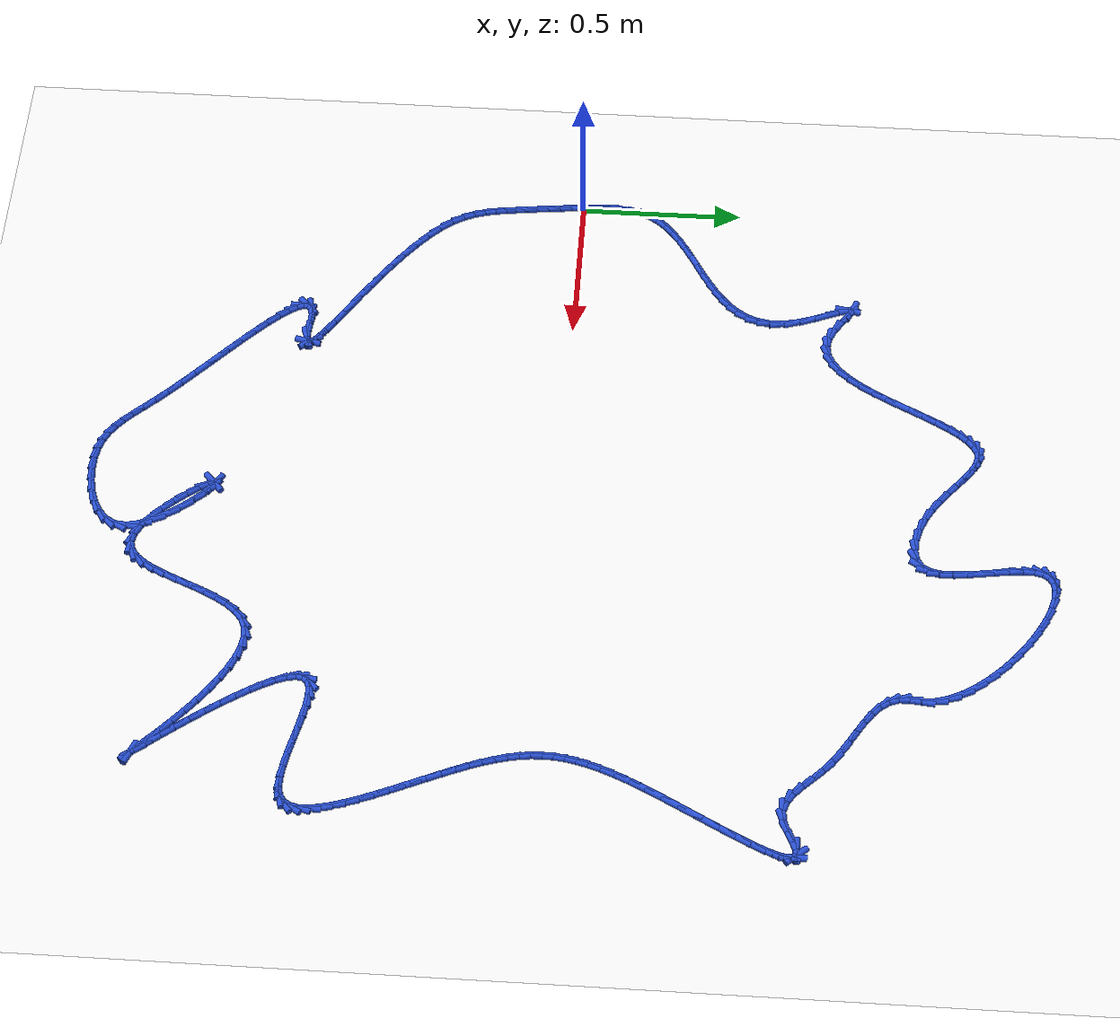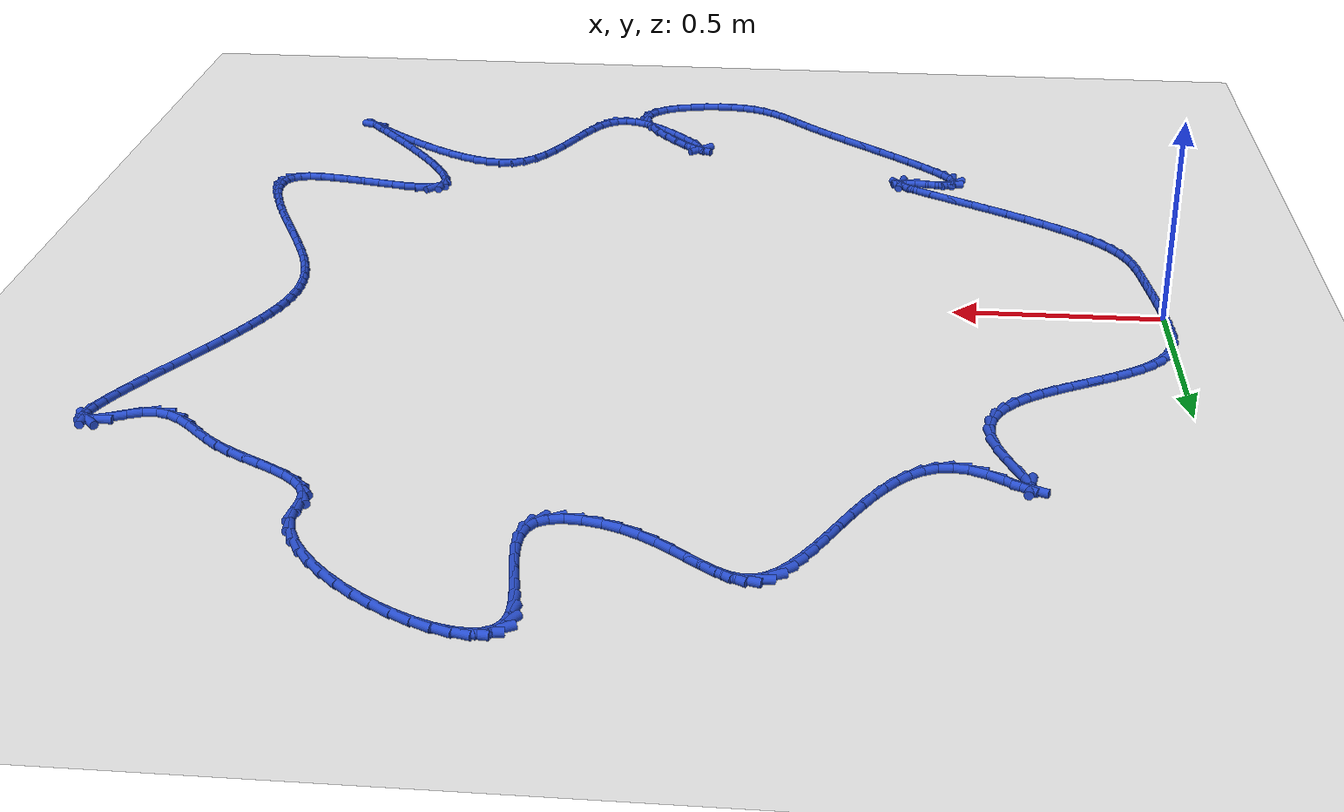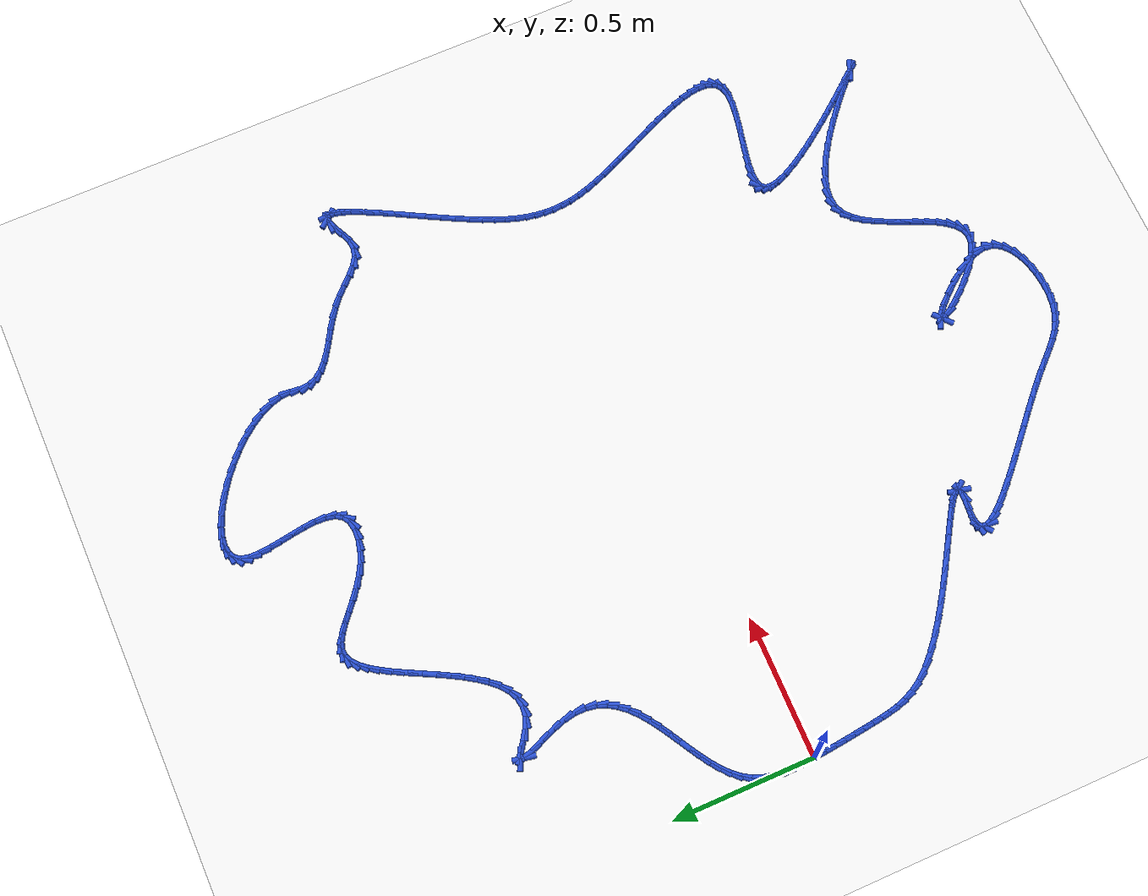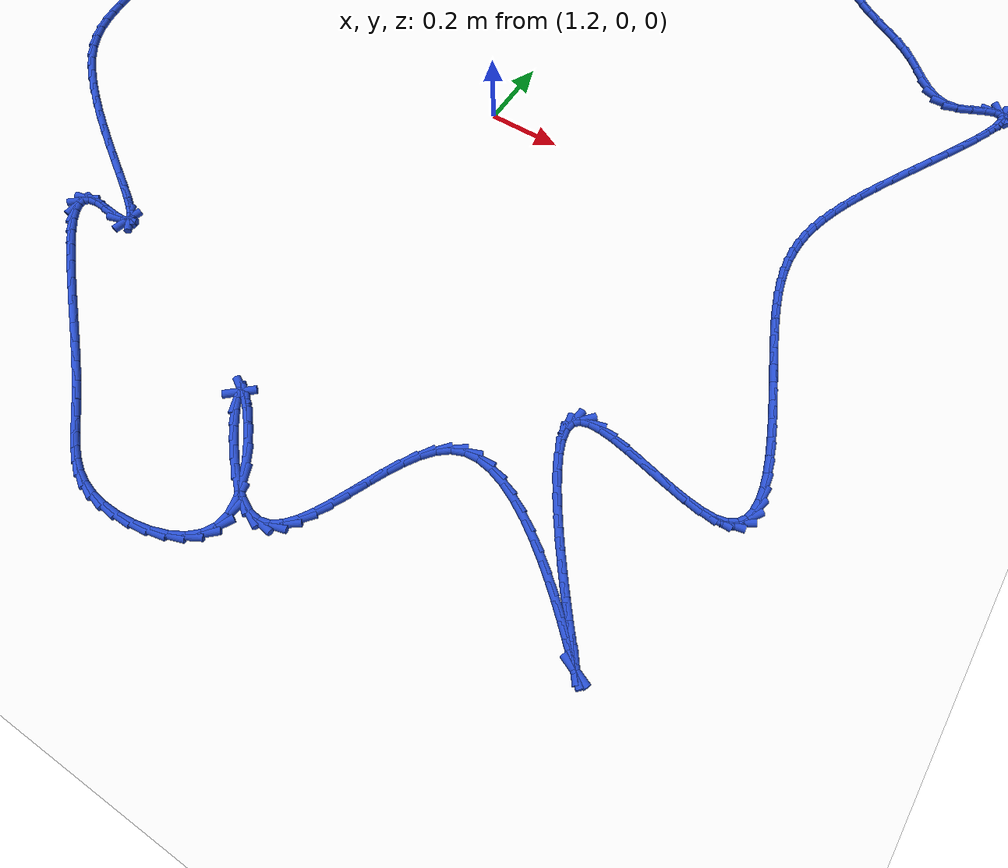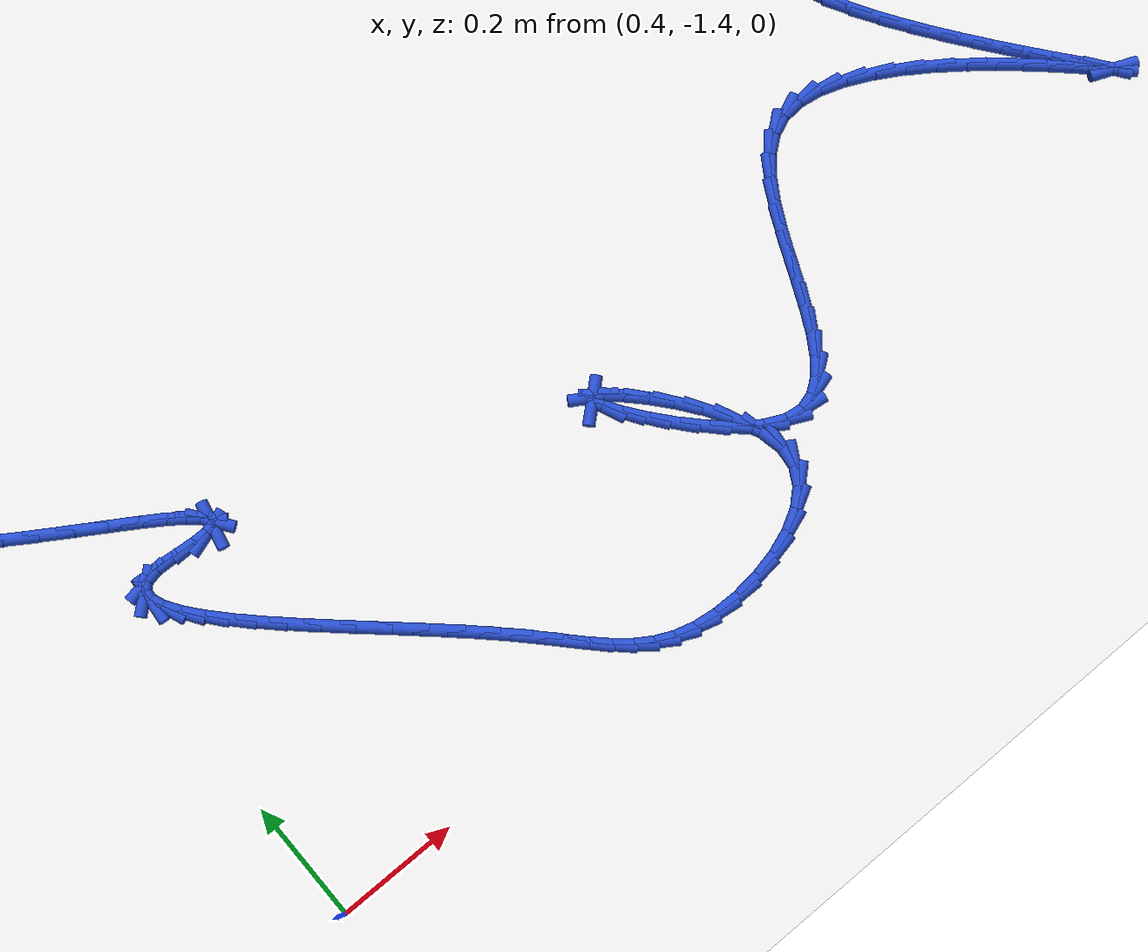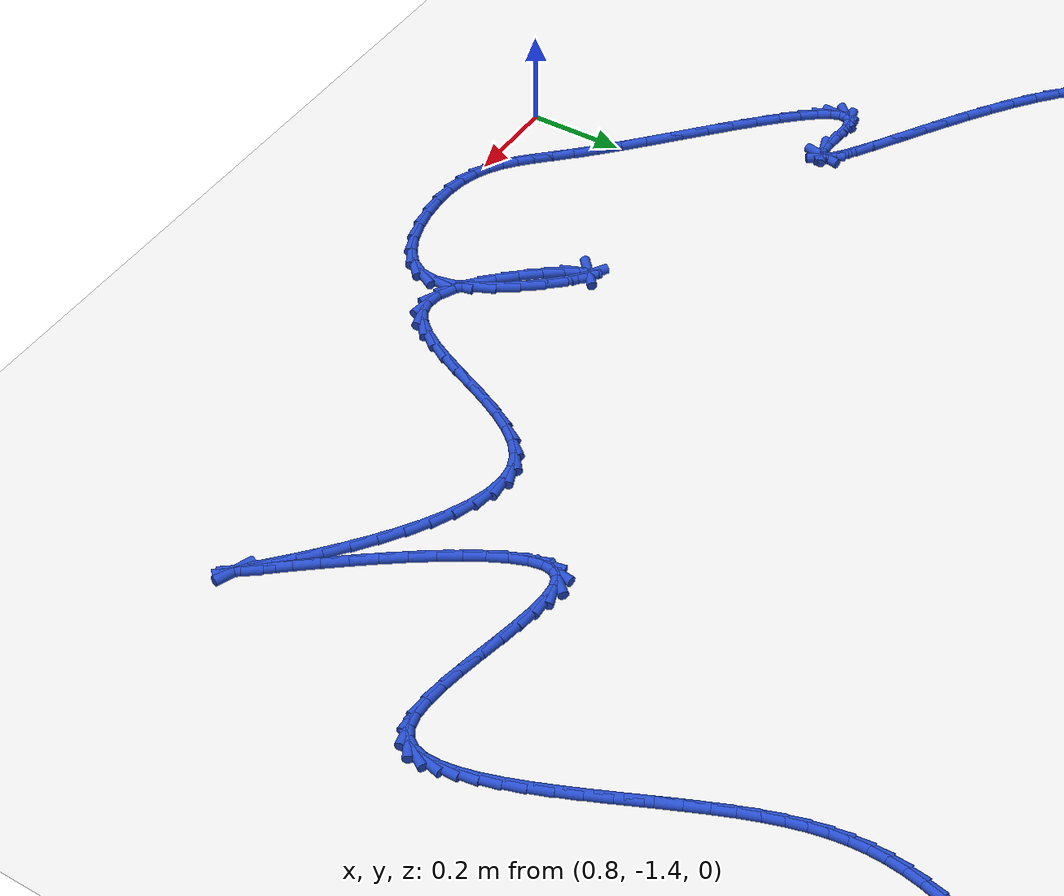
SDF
<sdf version="1.6">
 <world name="default">
  <light name="sun" type="directional">
   <pose>0 0 10 0 -0 0</pose>
   <diffuse>0.8 0.8 0.8 1</diffuse>
   <specular>0.2 0.2 0.2 1</specular>
   <attenuation>
    <range>1000</range>
    <constant>0.9</constant>
    <linear>0.01</linear>
    <quadratic>0.001</quadratic>
   </attenuation>
   <direction>-0.5 0.1 -0.9</direction>
  </light>
  <model name="ground_plane">
   <static>1</static>
   <link name="link">
    <collision name="collision">
     <geometry><plane><normal>0 0 1</normal><size>100 100</size></plane></geometry>
     <surface><friction><ode><mu>100</mu><mu2>50</mu2></ode></friction></surface>
    </collision>
    <visual name="visual">
     <cast_shadows>0</cast_shadows>
     <geometry><plane><normal>0 0 1</normal><size>100 100</size></plane></geometry>
     <material>
      <script><uri>file://media/materials/scripts/gazebo.material</uri><name>Gazebo/WhiteGlow</name></script>
     </material>
    </visual>
   </link>
  </model>
  <gravity>0 0 -9.8</gravity>
  <magnetic_field>6e-06 2.3e-05 -4.2e-05</magnetic_field>
  <atmosphere type="adiabatic"/>
  <physics name="default_physics" default="0" type="ode">
   <max_step_size>0.001</max_step_size>
   <real_time_factor>1</real_time_factor>
   <real_time_update_rate>1000</real_time_update_rate>
  </physics>
  <scene><ambient>0.4 0.4 0.4 1</ambient><background>0.7 0.7 0.7 1</background><shadows>1</shadows></scene>
  <spherical_coordinates>
   <surface_model>EARTH_WGS84</surface_model>
   <latitude_deg>0</latitude_deg>
   <longitude_deg>0</longitude_deg>
   <elevation>0</elevation>
   <heading_deg>0</heading_deg>
  </spherical_coordinates>
  <model name="line">
   <link name="link_0">
    <pose>-3.469446951953614e-18 -4.85722573273506e-17 0.01 0 1.57 -1.5035557970851146</pose>
    <collision name="collision">
     <geometry><cylinder><radius>0.01</radius><length>0.08</length></cylinder></geometry>
    </collision>
    <visual name="visual">
     <material>
      <script><name>Gazebo/Blue</name><uri>file://media/materials/scripts/gazebo.material</uri></script>
     </material>
     <geometry><cylinder><radius>0.01</radius><length>0.08</length></cylinder></geometry>
    </visual>
   </link>
   <link name="link_1">
    <pose>-0.002491275513340506 0.03699435146968724 0.01 0 1.57 -1.5390851107611019</pose>
    <collision name="collision">
     <geometry><cylinder><radius>0.01</radius><length>0.08</length></cylinder></geometry>
    </collision>
    <visual name="visual">
     <material>
      <script><name>Gazebo/Blue</name><uri>file://media/materials/scripts/gazebo.material</uri></script>
     </material>
     <geometry><cylinder><radius>0.01</radius><length>0.08</length></cylinder></geometry>
    </visual>
   </link>
   <link name="link_2">
    <pose>-0.003666950472739593 0.0740563438259258 0.01 0 1.57 1.544068257868982</pose>
    <collision name="collision">
     <geometry><cylinder><radius>0.01</radius><length>0.08</length></cylinder></geometry>
    </collision>
    <visual name="visual">
     <material>
      <script><name>Gazebo/Blue</name><uri>file://media/materials/scripts/gazebo.material</uri></script>
     </material>
     <geometry><cylinder><radius>0.01</radius><length>0.08</length></cylinder></geometry>
    </visual>
   </link>
   <link name="link_3">
    <pose>-0.002689838309753529 0.11060516727441508 0.01 0 1.57 1.4593685758182837</pose>
    <collision name="collision">
     <geometry><cylinder><radius>0.01</radius><length>0.08</length></cylinder></geometry>
    </collision>
    <visual name="visual">
     <material>
      <script><name>Gazebo/Blue</name><uri>file://media/materials/scripts/gazebo.material</uri></script>
     </material>
     <geometry><cylinder><radius>0.01</radius><length>0.08</length></cylinder></geometry>
    </visual>
   </link>
   <link name="link_4">
    <pose>0.0012772475440614248 0.14606001202085456 0.01 0 1.57 1.344029843109757</pose>
    <collision name="collision">
     <geometry><cylinder><radius>0.01</radius><length>0.08</length></cylinder></geometry>
    </collision>
    <visual name="visual">
     <material>
      <script><name>Gazebo/Blue</name><uri>file://media/materials/scripts/gazebo.material</uri></script>
     </material>
     <geometry><cylinder><radius>0.01</radius><length>0.08</length></cylinder></geometry>
    </visual>
   </link>
   <link name="link_5">
    <pose>0.009071493657149004 0.1798400682709437 0.01 0 1.57 1.1944312286605236</pose>
    <collision name="collision">
     <geometry><cylinder><radius>0.01</radius><length>0.08</length></cylinder></geometry>
    </collision>
    <visual name="visual">
     <material>
      <script><name>Gazebo/Blue</name><uri>file://media/materials/scripts/gazebo.material</uri></script>
     </material>
     <geometry><cylinder><radius>0.01</radius><length>0.08</length></cylinder></geometry>
    </visual>
   </link>
   <link name="link_6">
    <pose>0.021530086597952955 0.21136452623038188 0.01 0 1.57 1.0179082269758917</pose>
    <collision name="collision">
     <geometry><cylinder><radius>0.01</radius><length>0.08</length></cylinder></geometry>
    </collision>
    <visual name="visual">
     <material>
      <script><name>Gazebo/Blue</name><uri>file://media/materials/scripts/gazebo.material</uri></script>
     </material>
     <geometry><cylinder><radius>0.01</radius><length>0.08</length></cylinder></geometry>
    </visual>
   </link>
   <link name="link_7">
    <pose>0.039303809747562375 0.24016719398791558 0.01 0 1.57 0.8589541591372676</pose>
    <collision name="collision">
     <geometry><cylinder><radius>0.01</radius><length>0.08</length></cylinder></geometry>
    </collision>
    <visual name="visual">
     <material>
      <script><name>Gazebo/Blue</name><uri>file://media/materials/scripts/gazebo.material</uri></script>
     </material>
     <geometry><cylinder><radius>0.01</radius><length>0.08</length></cylinder></geometry>
    </visual>
   </link>
   <link name="link_8">
    <pose>0.06197130474744068 0.26644113132356484 0.01 0 1.57 0.7347092351452045</pose>
    <collision name="collision">
     <geometry><cylinder><radius>0.01</radius><length>0.08</length></cylinder></geometry>
    </collision>
    <visual name="visual">
     <material>
      <script><name>Gazebo/Blue</name><uri>file://media/materials/scripts/gazebo.material</uri></script>
     </material>
     <geometry><cylinder><radius>0.01</radius><length>0.08</length></cylinder></geometry>
    </visual>
   </link>
   <link name="link_9">
    <pose>0.08872865000689141 0.29061463319988096 0.01 0 1.57 0.6428521692637451</pose>
    <collision name="collision">
     <geometry><cylinder><radius>0.01</radius><length>0.08</length></cylinder></geometry>
    </collision>
    <visual name="visual">
     <material>
      <script><name>Gazebo/Blue</name><uri>file://media/materials/scripts/gazebo.material</uri></script>
     </material>
     <geometry><cylinder><radius>0.01</radius><length>0.08</length></cylinder></geometry>
    </visual>
   </link>
   <link name="link_10">
    <pose>0.11877145031334191 0.3131162858058559 0.01 0 1.57 0.5789189315583009</pose>
    <collision name="collision">
     <geometry><cylinder><radius>0.01</radius><length>0.08</length></cylinder></geometry>
    </collision>
    <visual name="visual">
     <material>
      <script><name>Gazebo/Blue</name><uri>file://media/materials/scripts/gazebo.material</uri></script>
     </material>
     <geometry><cylinder><radius>0.01</radius><length>0.08</length></cylinder></geometry>
    </visual>
   </link>
   <link name="link_11">
    <pose>0.1512953104542196 0.334374675330482 0.01 0 1.57 0.5387709633680576</pose>
    <collision name="collision">
     <geometry><cylinder><radius>0.01</radius><length>0.08</length></cylinder></geometry>
    </collision>
    <visual name="visual">
     <material>
      <script><name>Gazebo/Blue</name><uri>file://media/materials/scripts/gazebo.material</uri></script>
     </material>
     <geometry><cylinder><radius>0.01</radius><length>0.08</length></cylinder></geometry>
    </visual>
   </link>
   <link name="link_12">
    <pose>0.1854958352169517 0.35481838796275145 0.01 0 1.57 0.519490489495759</pose>
    <collision name="collision">
     <geometry><cylinder><radius>0.01</radius><length>0.08</length></cylinder></geometry>
    </collision>
    <visual name="visual">
     <material>
      <script><name>Gazebo/Blue</name><uri>file://media/materials/scripts/gazebo.material</uri></script>
     </material>
     <geometry><cylinder><radius>0.01</radius><length>0.08</length></cylinder></geometry>
    </visual>
   </link>
   <link name="link_13">
    <pose>0.22056862938896565 0.37487600989165637 0.01 0 1.57 0.5195693823373988</pose>
    <collision name="collision">
     <geometry><cylinder><radius>0.01</radius><length>0.08</length></cylinder></geometry>
    </collision>
    <visual name="visual">
     <material>
      <script><name>Gazebo/Blue</name><uri>file://media/materials/scripts/gazebo.material</uri></script>
     </material>
     <geometry><cylinder><radius>0.01</radius><length>0.08</length></cylinder></geometry>
    </visual>
   </link>
   <link name="link_14">
    <pose>0.25570929775768875 0.3949761273061889 0.01 0 1.57 0.5388944939510351</pose>
    <collision name="collision">
     <geometry><cylinder><radius>0.01</radius><length>0.08</length></cylinder></geometry>
    </collision>
    <visual name="visual">
     <material>
      <script><name>Gazebo/Blue</name><uri>file://media/materials/scripts/gazebo.material</uri></script>
     </material>
     <geometry><cylinder><radius>0.01</radius><length>0.08</length></cylinder></geometry>
    </visual>
   </link>
   <link name="link_15">
    <pose>0.2901134451105483 0.4155473263953413 0.01 0 1.57 0.5787196924934523</pose>
    <collision name="collision">
     <geometry><cylinder><radius>0.01</radius><length>0.08</length></cylinder></geometry>
    </collision>
    <visual name="visual">
     <material>
      <script><name>Gazebo/Blue</name><uri>file://media/materials/scripts/gazebo.material</uri></script>
     </material>
     <geometry><cylinder><radius>0.01</radius><length>0.08</length></cylinder></geometry>
    </visual>
   </link>
   <link name="link_16">
    <pose>0.3229766762349717 0.43701819334810554 0.01 0 1.57 0.6416253466932331</pose>
    <collision name="collision">
     <geometry><cylinder><radius>0.01</radius><length>0.08</length></cylinder></geometry>
    </collision>
    <visual name="visual">
     <material>
      <script><name>Gazebo/Blue</name><uri>file://media/materials/scripts/gazebo.material</uri></script>
     </material>
     <geometry><cylinder><radius>0.01</radius><length>0.08</length></cylinder></geometry>
    </visual>
   </link>
   <link name="link_17">
    <pose>0.3534945959183864 0.45981731435347417 0.01 0 1.57 0.7312902869597495</pose>
    <collision name="collision">
     <geometry><cylinder><radius>0.01</radius><length>0.08</length></cylinder></geometry>
    </collision>
    <visual name="visual">
     <material>
      <script><name>Gazebo/Blue</name><uri>file://media/materials/scripts/gazebo.material</uri></script>
     </material>
     <geometry><cylinder><radius>0.01</radius><length>0.08</length></cylinder></geometry>
    </visual>
   </link>
   <link name="link_18">
    <pose>0.38086280894821944 0.48437327560043886 0.01 0 1.57 0.8516403191764031</pose>
    <collision name="collision">
     <geometry><cylinder><radius>0.01</radius><length>0.08</length></cylinder></geometry>
    </collision>
    <visual name="visual">
     <material>
      <script><name>Gazebo/Blue</name><uri>file://media/materials/scripts/gazebo.material</uri></script>
     </material>
     <geometry><cylinder><radius>0.01</radius><length>0.08</length></cylinder></geometry>
    </visual>
   </link>
   <link name="link_19">
    <pose>0.4042769201118985 0.5111146632779923 0.01 0 1.57 1.0046758146772399</pose>
    <collision name="collision">
     <geometry><cylinder><radius>0.01</radius><length>0.08</length></cylinder></geometry>
    </collision>
    <visual name="visual">
     <material>
      <script><name>Gazebo/Blue</name><uri>file://media/materials/scripts/gazebo.material</uri></script>
     </material>
     <geometry><cylinder><radius>0.01</radius><length>0.08</length></cylinder></geometry>
    </visual>
   </link>
   <link name="link_20">
    <pose>0.4229325341968506 0.5404700635751262 0.01 0 1.57 1.1867421542903942</pose>
    <collision name="collision">
     <geometry><cylinder><radius>0.01</radius><length>0.08</length></cylinder></geometry>
    </collision>
    <visual name="visual">
     <material>
      <script><name>Gazebo/Blue</name><uri>file://media/materials/scripts/gazebo.material</uri></script>
     </material>
     <geometry><cylinder><radius>0.01</radius><length>0.08</length></cylinder></geometry>
    </visual>
   </link>
   <link name="link_21">
    <pose>0.43602525599050346 0.5728680626808331 0.01 0 1.57 1.3854493929418508</pose>
    <collision name="collision">
     <geometry><cylinder><radius>0.01</radius><length>0.08</length></cylinder></geometry>
    </collision>
    <visual name="visual">
     <material>
      <script><name>Gazebo/Blue</name><uri>file://media/materials/scripts/gazebo.material</uri></script>
     </material>
     <geometry><cylinder><radius>0.01</radius><length>0.08</length></cylinder></geometry>
    </visual>
   </link>
   <link name="link_22">
    <pose>0.4427506902802841 0.608737246784105 0.01 0 1.57 -1.5595757730847697</pose>
    <collision name="collision">
     <geometry><cylinder><radius>0.01</radius><length>0.08</length></cylinder></geometry>
    </collision>
    <visual name="visual">
     <material>
      <script><name>Gazebo/Blue</name><uri>file://media/materials/scripts/gazebo.material</uri></script>
     </material>
     <geometry><cylinder><radius>0.01</radius><length>0.08</length></cylinder></geometry>
    </visual>
   </link>
   <link name="link_23">
    <pose>0.44230444185361995 0.648506202073934 0.01 0 1.57 -1.3822785067163863</pose>
    <collision name="collision">
     <geometry><cylinder><radius>0.01</radius><length>0.08</length></cylinder></geometry>
    </collision>
    <visual name="visual">
     <material>
      <script><name>Gazebo/Blue</name><uri>file://media/materials/scripts/gazebo.material</uri></script>
     </material>
     <geometry><cylinder><radius>0.01</radius><length>0.08</length></cylinder></geometry>
    </visual>
   </link>
   <link name="link_24">
    <pose>0.43389350201613186 0.6925925608759059 0.01 0 1.57 -1.2538148254085466</pose>
    <collision name="collision">
     <geometry><cylinder><radius>0.01</radius><length>0.08</length></cylinder></geometry>
    </collision>
    <visual name="visual">
     <material>
      <script><name>Gazebo/Blue</name><uri>file://media/materials/scripts/gazebo.material</uri></script>
     </material>
     <geometry><cylinder><radius>0.01</radius><length>0.08</length></cylinder></geometry>
    </visual>
   </link>
   <link name="link_25">
    <pose>0.4184096928314629 0.7397931434576318 0.01 0 1.57 -1.1922383402729906</pose>
    <collision name="collision">
     <geometry><cylinder><radius>0.01</radius><length>0.08</length></cylinder></geometry>
    </collision>
    <visual name="visual">
     <material>
      <script><name>Gazebo/Blue</name><uri>file://media/materials/scripts/gazebo.material</uri></script>
     </material>
     <geometry><cylinder><radius>0.01</radius><length>0.08</length></cylinder></geometry>
    </visual>
   </link>
   <link name="link_26">
    <pose>0.400196758983007 0.7855840105512915 0.01 0 1.57 -1.1816825938432873</pose>
    <collision name="collision">
     <geometry><cylinder><radius>0.01</radius><length>0.08</length></cylinder></geometry>
    </collision>
    <visual name="visual">
     <material>
      <script><name>Gazebo/Blue</name><uri>file://media/materials/scripts/gazebo.material</uri></script>
     </material>
     <geometry><cylinder><radius>0.01</radius><length>0.08</length></cylinder></geometry>
    </visual>
   </link>
   <link name="link_27">
    <pose>0.3840213402727948 0.8250343965628721 0.01 0 1.57 -1.2497416400634016</pose>
    <collision name="collision">
     <geometry><cylinder><radius>0.01</radius><length>0.08</length></cylinder></geometry>
    </collision>
    <visual name="visual">
     <material>
      <script><name>Gazebo/Blue</name><uri>file://media/materials/scripts/gazebo.material</uri></script>
     </material>
     <geometry><cylinder><radius>0.01</radius><length>0.08</length></cylinder></geometry>
    </visual>
   </link>
   <link name="link_28">
    <pose>0.37465007650285614 0.8532135358983607 0.01 0 1.57 1.3891757259824857</pose>
    <collision name="collision">
     <geometry><cylinder><radius>0.01</radius><length>0.08</length></cylinder></geometry>
    </collision>
    <visual name="visual">
     <material>
      <script><name>Gazebo/Blue</name><uri>file://media/materials/scripts/gazebo.material</uri></script>
     </material>
     <geometry><cylinder><radius>0.01</radius><length>0.08</length></cylinder></geometry>
    </visual>
   </link>
   <link name="link_29">
    <pose>0.37684960747522167 0.8651906629637433 0.01 0 1.57 -0.41789258580121025</pose>
    <collision name="collision">
     <geometry><cylinder><radius>0.01</radius><length>0.08</length></cylinder></geometry>
    </collision>
    <visual name="visual">
     <material>
      <script><name>Gazebo/Blue</name><uri>file://media/materials/scripts/gazebo.material</uri></script>
     </material>
     <geometry><cylinder><radius>0.01</radius><length>0.08</length></cylinder></geometry>
    </visual>
   </link>
   <link name="link_30">
    <pose>0.39445333956255335 0.8573737745000473 0.01 0 1.57 -0.6175390298586856</pose>
    <collision name="collision">
     <geometry><cylinder><radius>0.01</radius><length>0.08</length></cylinder></geometry>
    </collision>
    <visual name="visual">
     <material>
      <script><name>Gazebo/Blue</name><uri>file://media/materials/scripts/gazebo.material</uri></script>
     </material>
     <geometry><cylinder><radius>0.01</radius><length>0.08</length></cylinder></geometry>
    </visual>
   </link>
   <link name="link_31">
    <pose>0.4243391507244915 0.8361488632851112 0.01 0 1.57 -0.5842321517447974</pose>
    <collision name="collision">
     <geometry><cylinder><radius>0.01</radius><length>0.08</length></cylinder></geometry>
    </collision>
    <visual name="visual">
     <material>
      <script><name>Gazebo/Blue</name><uri>file://media/materials/scripts/gazebo.material</uri></script>
     </material>
     <geometry><cylinder><radius>0.01</radius><length>0.08</length></cylinder></geometry>
    </visual>
   </link>
   <link name="link_32">
    <pose>0.46024445062688446 0.8124070550397324 0.01 0 1.57 -0.41734542980720046</pose>
    <collision name="collision">
     <geometry><cylinder><radius>0.01</radius><length>0.08</length></cylinder></geometry>
    </collision>
    <visual name="visual">
     <material>
      <script><name>Gazebo/Blue</name><uri>file://media/materials/scripts/gazebo.material</uri></script>
     </material>
     <geometry><cylinder><radius>0.01</radius><length>0.08</length></cylinder></geometry>
    </visual>
   </link>
   <link name="link_33">
    <pose>0.49621227974537485 0.7964591949227914 0.01 0 1.57 -0.14137503615323826</pose>
    <collision name="collision">
     <geometry><cylinder><radius>0.01</radius><length>0.08</length></cylinder></geometry>
    </collision>
    <visual name="visual">
     <material>
      <script><name>Gazebo/Blue</name><uri>file://media/materials/scripts/gazebo.material</uri></script>
     </material>
     <geometry><cylinder><radius>0.01</radius><length>0.08</length></cylinder></geometry>
    </visual>
   </link>
   <link name="link_34">
    <pose>0.5299976168033949 0.7916507133591806 0.01 0 1.57 0.16235223265066762</pose>
    <collision name="collision">
     <geometry><cylinder><radius>0.01</radius><length>0.08</length></cylinder></geometry>
    </collision>
    <visual name="visual">
     <material>
      <script><name>Gazebo/Blue</name><uri>file://media/materials/scripts/gazebo.material</uri></script>
     </material>
     <geometry><cylinder><radius>0.01</radius><length>0.08</length></cylinder></geometry>
    </visual>
   </link>
   <link name="link_35">
    <pose>0.5617412339717663 0.7968501234003461 0.01 0 1.57 0.43819260171617636</pose>
    <collision name="collision">
     <geometry><cylinder><radius>0.01</radius><length>0.08</length></cylinder></geometry>
    </collision>
    <visual name="visual">
     <material>
      <script><name>Gazebo/Blue</name><uri>file://media/materials/scripts/gazebo.material</uri></script>
     </material>
     <geometry><cylinder><radius>0.01</radius><length>0.08</length></cylinder></geometry>
    </visual>
   </link>
   <link name="link_36">
    <pose>0.59162326400468 0.8108520783594951 0.01 0 1.57 0.6536071172656929</pose>
    <collision name="collision">
     <geometry><cylinder><radius>0.01</radius><length>0.08</length></cylinder></geometry>
    </collision>
    <visual name="visual">
     <material>
      <script><name>Gazebo/Blue</name><uri>file://media/materials/scripts/gazebo.material</uri></script>
     </material>
     <geometry><cylinder><radius>0.01</radius><length>0.08</length></cylinder></geometry>
    </visual>
   </link>
   <link name="link_37">
    <pose>0.6198238396563265 0.8324512315498346 0.01 0 1.57 0.8090131655517493</pose>
    <collision name="collision">
     <geometry><cylinder><radius>0.01</radius><length>0.08</length></cylinder></geometry>
    </collision>
    <visual name="visual">
     <material>
      <script><name>Gazebo/Blue</name><uri>file://media/materials/scripts/gazebo.material</uri></script>
     </material>
     <geometry><cylinder><radius>0.01</radius><length>0.08</length></cylinder></geometry>
    </visual>
   </link>
   <link name="link_38">
    <pose>0.6465230936808962 0.8604422362845714 0.01 0 1.57 0.9178160358527657</pose>
    <collision name="collision">
     <geometry><cylinder><radius>0.01</radius><length>0.08</length></cylinder></geometry>
    </collision>
    <visual name="visual">
     <material>
      <script><name>Gazebo/Blue</name><uri>file://media/materials/scripts/gazebo.material</uri></script>
     </material>
     <geometry><cylinder><radius>0.01</radius><length>0.08</length></cylinder></geometry>
    </visual>
   </link>
   <link name="link_39">
    <pose>0.6719011588325806 0.8936197458769135 0.01 0 1.57 0.992835950291742</pose>
    <collision name="collision">
     <geometry><cylinder><radius>0.01</radius><length>0.08</length></cylinder></geometry>
    </collision>
    <visual name="visual">
     <material>
      <script><name>Gazebo/Blue</name><uri>file://media/materials/scripts/gazebo.material</uri></script>
     </material>
     <geometry><cylinder><radius>0.01</radius><length>0.08</length></cylinder></geometry>
    </visual>
   </link>
   <link name="link_40">
    <pose>0.69613816786557 0.9307784136400675 0.01 0 1.57 1.0430774463765724</pose>
    <collision name="collision">
     <geometry><cylinder><radius>0.01</radius><length>0.08</length></cylinder></geometry>
    </collision>
    <visual name="visual">
     <material>
      <script><name>Gazebo/Blue</name><uri>file://media/materials/scripts/gazebo.material</uri></script>
     </material>
     <geometry><cylinder><radius>0.01</radius><length>0.08</length></cylinder></geometry>
    </visual>
   </link>
   <link name="link_41">
    <pose>0.7194142535340554 0.9707128928872408 0.01 0 1.57 1.074123053864128</pose>
    <collision name="collision">
     <geometry><cylinder><radius>0.01</radius><length>0.08</length></cylinder></geometry>
    </collision>
    <visual name="visual">
     <material>
      <script><name>Gazebo/Blue</name><uri>file://media/materials/scripts/gazebo.material</uri></script>
     </material>
     <geometry><cylinder><radius>0.01</radius><length>0.08</length></cylinder></geometry>
    </visual>
   </link>
   <link name="link_42">
    <pose>0.7419095485922274 1.0122178369316404 0.01 0 1.57 1.0889823387279105</pose>
    <collision name="collision">
     <geometry><cylinder><radius>0.01</radius><length>0.08</length></cylinder></geometry>
    </collision>
    <visual name="visual">
     <material>
      <script><name>Gazebo/Blue</name><uri>file://media/materials/scripts/gazebo.material</uri></script>
     </material>
     <geometry><cylinder><radius>0.01</radius><length>0.08</length></cylinder></geometry>
    </visual>
   </link>
   <link name="link_43">
    <pose>0.7638041857942766 1.0540878990864733 0.01 0 1.57 1.088621710138873</pose>
    <collision name="collision">
     <geometry><cylinder><radius>0.01</radius><length>0.08</length></cylinder></geometry>
    </collision>
    <visual name="visual">
     <material>
      <script><name>Gazebo/Blue</name><uri>file://media/materials/scripts/gazebo.material</uri></script>
     </material>
     <geometry><cylinder><radius>0.01</radius><length>0.08</length></cylinder></geometry>
    </visual>
   </link>
   <link name="link_44">
    <pose>0.7852782978943937 1.095117732664947 0.01 0 1.57 1.072051214306616</pose>
    <collision name="collision">
     <geometry><cylinder><radius>0.01</radius><length>0.08</length></cylinder></geometry>
    </collision>
    <visual name="visual">
     <material>
      <script><name>Gazebo/Blue</name><uri>file://media/materials/scripts/gazebo.material</uri></script>
     </material>
     <geometry><cylinder><radius>0.01</radius><length>0.08</length></cylinder></geometry>
    </visual>
   </link>
   <link name="link_45">
    <pose>0.8065120176467699 1.1341019909802688 0.01 0 1.57 1.0358795764966506</pose>
    <collision name="collision">
     <geometry><cylinder><radius>0.01</radius><length>0.08</length></cylinder></geometry>
    </collision>
    <visual name="visual">
     <material>
      <script><name>Gazebo/Blue</name><uri>file://media/materials/scripts/gazebo.material</uri></script>
     </material>
     <geometry><cylinder><radius>0.01</radius><length>0.08</length></cylinder></geometry>
    </visual>
   </link>
   <link name="link_46">
    <pose>0.8276854778055959 1.1698353273456457 0.01 0 1.57 0.973074888336738</pose>
    <collision name="collision">
     <geometry><cylinder><radius>0.01</radius><length>0.08</length></cylinder></geometry>
    </collision>
    <visual name="visual">
     <material>
      <script><name>Gazebo/Blue</name><uri>file://media/materials/scripts/gazebo.material</uri></script>
     </material>
     <geometry><cylinder><radius>0.01</radius><length>0.08</length></cylinder></geometry>
    </visual>
   </link>
   <link name="link_47">
    <pose>0.8489788111250622 1.2011123950742846 0.01 0 1.57 0.8703913042534615</pose>
    <collision name="collision">
     <geometry><cylinder><radius>0.01</radius><length>0.08</length></cylinder></geometry>
    </collision>
    <visual name="visual">
     <material>
      <script><name>Gazebo/Blue</name><uri>file://media/materials/scripts/gazebo.material</uri></script>
     </material>
     <geometry><cylinder><radius>0.01</radius><length>0.08</length></cylinder></geometry>
    </visual>
   </link>
   <link name="link_48">
    <pose>0.8705721503593595 1.226727847479393 0.01 0 1.57 0.7041266363398381</pose>
    <collision name="collision">
     <geometry><cylinder><radius>0.01</radius><length>0.08</length></cylinder></geometry>
    </collision>
    <visual name="visual">
     <material>
      <script><name>Gazebo/Blue</name><uri>file://media/materials/scripts/gazebo.material</uri></script>
     </material>
     <geometry><cylinder><radius>0.01</radius><length>0.08</length></cylinder></geometry>
    </visual>
   </link>
   <link name="link_49">
    <pose>0.8926456282626789 1.245476337874178 0.01 0 1.57 0.439048094520214</pose>
    <collision name="collision">
     <geometry><cylinder><radius>0.01</radius><length>0.08</length></cylinder></geometry>
    </collision>
    <visual name="visual">
     <material>
      <script><name>Gazebo/Blue</name><uri>file://media/materials/scripts/gazebo.material</uri></script>
     </material>
     <geometry><cylinder><radius>0.01</radius><length>0.08</length></cylinder></geometry>
    </visual>
   </link>
   <link name="link_50">
    <pose>0.9153793775892112 1.256152519571847 0.01 0 1.57 0.06250082210837357</pose>
    <collision name="collision">
     <geometry><cylinder><radius>0.01</radius><length>0.08</length></cylinder></geometry>
    </collision>
    <visual name="visual">
     <material>
      <script><name>Gazebo/Blue</name><uri>file://media/materials/scripts/gazebo.material</uri></script>
     </material>
     <geometry><cylinder><radius>0.01</radius><length>0.08</length></cylinder></geometry>
    </visual>
   </link>
   <link name="link_51">
    <pose>0.938954292927347 1.2576278927714963 0.01 0 1.57 -0.2907933008298742</pose>
    <collision name="collision">
     <geometry><cylinder><radius>0.01</radius><length>0.08</length></cylinder></geometry>
    </collision>
    <visual name="visual">
     <material>
      <script><name>Gazebo/Blue</name><uri>file://media/materials/scripts/gazebo.material</uri></script>
     </material>
     <geometry><cylinder><radius>0.01</radius><length>0.08</length></cylinder></geometry>
    </visual>
   </link>
   <link name="link_52">
    <pose>0.9635660224999892 1.2502621697616816 0.01 0 1.57 -0.5110485343310961</pose>
    <collision name="collision">
     <geometry><cylinder><radius>0.01</radius><length>0.08</length></cylinder></geometry>
    </collision>
    <visual name="visual">
     <material>
      <script><name>Gazebo/Blue</name><uri>file://media/materials/scripts/gazebo.material</uri></script>
     </material>
     <geometry><cylinder><radius>0.01</radius><length>0.08</length></cylinder></geometry>
    </visual>
   </link>
   <link name="link_53">
    <pose>0.9894235765848806 1.2357629050552201 0.01 0 1.57 -0.6290993567731736</pose>
    <collision name="collision">
     <geometry><cylinder><radius>0.01</radius><length>0.08</length></cylinder></geometry>
    </collision>
    <visual name="visual">
     <material>
      <script><name>Gazebo/Blue</name><uri>file://media/materials/scripts/gazebo.material</uri></script>
     </material>
     <geometry><cylinder><radius>0.01</radius><length>0.08</length></cylinder></geometry>
    </visual>
   </link>
   <link name="link_54">
    <pose>1.0167364481214298 1.2158863396717536 0.01 0 1.57 -0.6813441813651456</pose>
    <collision name="collision">
     <geometry><cylinder><radius>0.01</radius><length>0.08</length></cylinder></geometry>
    </collision>
    <visual name="visual">
     <material>
      <script><name>Gazebo/Blue</name><uri>file://media/materials/scripts/gazebo.material</uri></script>
     </material>
     <geometry><cylinder><radius>0.01</radius><length>0.08</length></cylinder></geometry>
    </visual>
   </link>
   <link name="link_55">
    <pose>1.0457141300490471 1.1923887146309264 0.01 0 1.57 -0.6880532109664231</pose>
    <collision name="collision">
     <geometry><cylinder><radius>0.01</radius><length>0.08</length></cylinder></geometry>
    </collision>
    <visual name="visual">
     <material>
      <script><name>Gazebo/Blue</name><uri>file://media/materials/scripts/gazebo.material</uri></script>
     </material>
     <geometry><cylinder><radius>0.01</radius><length>0.08</length></cylinder></geometry>
    </visual>
   </link>
   <link name="link_56">
    <pose>1.0765661153071422 1.1670262709523809 0.01 0 1.57 -0.6582809554437344</pose>
    <collision name="collision">
     <geometry><cylinder><radius>0.01</radius><length>0.08</length></cylinder></geometry>
    </collision>
    <visual name="visual">
     <material>
      <script><name>Gazebo/Blue</name><uri>file://media/materials/scripts/gazebo.material</uri></script>
     </material>
     <geometry><cylinder><radius>0.01</radius><length>0.08</length></cylinder></geometry>
    </visual>
   </link>
   <link name="link_57">
    <pose>1.1095018968351245 1.1415552496557602 0.01 0 1.57 -0.5946020400388812</pose>
    <collision name="collision">
     <geometry><cylinder><radius>0.01</radius><length>0.08</length></cylinder></geometry>
    </collision>
    <visual name="visual">
     <material>
      <script><name>Gazebo/Blue</name><uri>file://media/materials/scripts/gazebo.material</uri></script>
     </material>
     <geometry><cylinder><radius>0.01</radius><length>0.08</length></cylinder></geometry>
    </visual>
   </link>
   <link name="link_58">
    <pose>1.1447309675724031 1.117731891760707 0.01 0 1.57 -0.49605298139443954</pose>
    <collision name="collision">
     <geometry><cylinder><radius>0.01</radius><length>0.08</length></cylinder></geometry>
    </collision>
    <visual name="visual">
     <material>
      <script><name>Gazebo/Blue</name><uri>file://media/materials/scripts/gazebo.material</uri></script>
     </material>
     <geometry><cylinder><radius>0.01</radius><length>0.08</length></cylinder></geometry>
    </visual>
   </link>
   <link name="link_59">
    <pose>1.182462104114913 1.0973122346371218 0.01 0 1.57 -0.37008091538841814</pose>
    <collision name="collision">
     <geometry><cylinder><radius>0.01</radius><length>0.08</length></cylinder></geometry>
    </collision>
    <visual name="visual">
     <material>
      <script><name>Gazebo/Blue</name><uri>file://media/materials/scripts/gazebo.material</uri></script>
     </material>
     <geometry><cylinder><radius>0.01</radius><length>0.08</length></cylinder></geometry>
    </visual>
   </link>
   <link name="link_60">
    <pose>1.2222647351839147 1.0818705550399248 0.01 0 1.57 -0.23302321920221766</pose>
    <collision name="collision">
     <geometry><cylinder><radius>0.01</radius><length>0.08</length></cylinder></geometry>
    </collision>
    <visual name="visual">
     <material>
      <script><name>Gazebo/Blue</name><uri>file://media/materials/scripts/gazebo.material</uri></script>
     </material>
     <geometry><cylinder><radius>0.01</radius><length>0.08</length></cylinder></geometry>
    </visual>
   </link>
   <link name="link_61">
    <pose>1.2618936461394727 1.0724652436057558 0.01 0 1.57 -0.06500561413143688</pose>
    <collision name="collision">
     <geometry><cylinder><radius>0.01</radius><length>0.08</length></cylinder></geometry>
    </collision>
    <visual name="visual">
     <material>
      <script><name>Gazebo/Blue</name><uri>file://media/materials/scripts/gazebo.material</uri></script>
     </material>
     <geometry><cylinder><radius>0.01</radius><length>0.08</length></cylinder></geometry>
    </visual>
   </link>
   <link name="link_62">
    <pose>1.2987838699629737 1.0700637883636246 0.01 0 1.57 0.17454288929553524</pose>
    <collision name="collision">
     <geometry><cylinder><radius>0.01</radius><length>0.08</length></cylinder></geometry>
    </collision>
    <visual name="visual">
     <material>
      <script><name>Gazebo/Blue</name><uri>file://media/materials/scripts/gazebo.material</uri></script>
     </material>
     <geometry><cylinder><radius>0.01</radius><length>0.08</length></cylinder></geometry>
    </visual>
   </link>
   <link name="link_63">
    <pose>1.3303704396358056 1.0756336773425434 0.01 0 1.57 0.5484654266116746</pose>
    <collision name="collision">
     <geometry><cylinder><radius>0.01</radius><length>0.08</length></cylinder></geometry>
    </collision>
    <visual name="visual">
     <material>
      <script><name>Gazebo/Blue</name><uri>file://media/materials/scripts/gazebo.material</uri></script>
     </material>
     <geometry><cylinder><radius>0.01</radius><length>0.08</length></cylinder></geometry>
    </visual>
   </link>
   <link name="link_64">
    <pose>1.3541020919847546 1.090133616776462 0.01 0 1.57 1.0114527236162802</pose>
    <collision name="collision">
     <geometry><cylinder><radius>0.01</radius><length>0.08</length></cylinder></geometry>
    </collision>
    <visual name="visual">
     <material>
      <script><name>Gazebo/Blue</name><uri>file://media/materials/scripts/gazebo.material</uri></script>
     </material>
     <geometry><cylinder><radius>0.01</radius><length>0.08</length></cylinder></geometry>
    </visual>
   </link>
   <link name="link_65">
    <pose>1.368814050372023 1.1136338147988292 0.01 0 1.57 1.3456189995589798</pose>
    <collision name="collision">
     <geometry><cylinder><radius>0.01</radius><length>0.08</length></cylinder></geometry>
    </collision>
    <visual name="visual">
     <material>
      <script><name>Gazebo/Blue</name><uri>file://media/materials/scripts/gazebo.material</uri></script>
     </material>
     <geometry><cylinder><radius>0.01</radius><length>0.08</length></cylinder></geometry>
    </visual>
   </link>
   <link name="link_66">
    <pose>1.3758993001423114 1.1445653964326998 0.01 0 1.57 1.5400175159806568</pose>
    <collision name="collision">
     <geometry><cylinder><radius>0.01</radius><length>0.08</length></cylinder></geometry>
    </collision>
    <visual name="visual">
     <material>
      <script><name>Gazebo/Blue</name><uri>file://media/materials/scripts/gazebo.material</uri></script>
     </material>
     <geometry><cylinder><radius>0.01</radius><length>0.08</length></cylinder></geometry>
    </visual>
   </link>
   <link name="link_67">
    <pose>1.377026693348663 1.1811827038474247 0.01 0 1.57 -1.4929996170355078</pose>
    <collision name="collision">
     <geometry><cylinder><radius>0.01</radius><length>0.08</length></cylinder></geometry>
    </collision>
    <visual name="visual">
     <material>
      <script><name>Gazebo/Blue</name><uri>file://media/materials/scripts/gazebo.material</uri></script>
     </material>
     <geometry><cylinder><radius>0.01</radius><length>0.08</length></cylinder></geometry>
    </visual>
   </link>
   <link name="link_68">
    <pose>1.3738650820441183 1.2217400792123556 0.01 0 1.57 -1.436371619667582</pose>
    <collision name="collision">
     <geometry><cylinder><radius>0.01</radius><length>0.08</length></cylinder></geometry>
    </collision>
    <visual name="visual">
     <material>
      <script><name>Gazebo/Blue</name><uri>file://media/materials/scripts/gazebo.material</uri></script>
     </material>
     <geometry><cylinder><radius>0.01</radius><length>0.08</length></cylinder></geometry>
    </visual>
   </link>
   <link name="link_69">
    <pose>1.3680833182817191 1.2644918646968437 0.01 0 1.57 -1.4161841920375353</pose>
    <collision name="collision">
     <geometry><cylinder><radius>0.01</radius><length>0.08</length></cylinder></geometry>
    </collision>
    <visual name="visual">
     <material>
      <script><name>Gazebo/Blue</name><uri>file://media/materials/scripts/gazebo.material</uri></script>
     </material>
     <geometry><cylinder><radius>0.01</radius><length>0.08</length></cylinder></geometry>
    </visual>
   </link>
   <link name="link_70">
    <pose>1.3613502541145073 1.3076924024702399 0.01 0 1.57 -1.428214583452618</pose>
    <collision name="collision">
     <geometry><cylinder><radius>0.01</radius><length>0.08</length></cylinder></geometry>
    </collision>
    <visual name="visual">
     <material>
      <script><name>Gazebo/Blue</name><uri>file://media/materials/scripts/gazebo.material</uri></script>
     </material>
     <geometry><cylinder><radius>0.01</radius><length>0.08</length></cylinder></geometry>
    </visual>
   </link>
   <link name="link_71">
    <pose>1.3553347415955237 1.3495960347018958 0.01 0 1.57 -1.4776796456335275</pose>
    <collision name="collision">
     <geometry><cylinder><radius>0.01</radius><length>0.08</length></cylinder></geometry>
    </collision>
    <visual name="visual">
     <material>
      <script><name>Gazebo/Blue</name><uri>file://media/materials/scripts/gazebo.material</uri></script>
     </material>
     <geometry><cylinder><radius>0.01</radius><length>0.08</length></cylinder></geometry>
    </visual>
   </link>
   <link name="link_72">
    <pose>1.3517056327778103 1.388457103561163 0.01 0 1.57 1.5582900425186175</pose>
    <collision name="collision">
     <geometry><cylinder><radius>0.01</radius><length>0.08</length></cylinder></geometry>
    </collision>
    <visual name="visual">
     <material>
      <script><name>Gazebo/Blue</name><uri>file://media/materials/scripts/gazebo.material</uri></script>
     </material>
     <geometry><cylinder><radius>0.01</radius><length>0.08</length></cylinder></geometry>
    </visual>
   </link>
   <link name="link_73">
    <pose>1.3521317797144086 1.4225299512173923 0.01 0 1.57 1.3510727814411303</pose>
    <collision name="collision">
     <geometry><cylinder><radius>0.01</radius><length>0.08</length></cylinder></geometry>
    </collision>
    <visual name="visual">
     <material>
      <script><name>Gazebo/Blue</name><uri>file://media/materials/scripts/gazebo.material</uri></script>
     </material>
     <geometry><cylinder><radius>0.01</radius><length>0.08</length></cylinder></geometry>
    </visual>
   </link>
   <link name="link_74">
    <pose>1.35828203445836 1.4500689198399352 0.01 0 1.57 0.972160265118087</pose>
    <collision name="collision">
     <geometry><cylinder><radius>0.01</radius><length>0.08</length></cylinder></geometry>
    </collision>
    <visual name="visual">
     <material>
      <script><name>Gazebo/Blue</name><uri>file://media/materials/scripts/gazebo.material</uri></script>
     </material>
     <geometry><cylinder><radius>0.01</radius><length>0.08</length></cylinder></geometry>
    </visual>
   </link>
   <link name="link_75">
    <pose>1.371571825449991 1.469551521705287 0.01 0 1.57 0.5154134863984006</pose>
    <collision name="collision">
     <geometry><cylinder><radius>0.01</radius><length>0.08</length></cylinder></geometry>
    </collision>
    <visual name="visual">
     <material>
      <script><name>Gazebo/Blue</name><uri>file://media/materials/scripts/gazebo.material</uri></script>
     </material>
     <geometry><cylinder><radius>0.01</radius><length>0.08</length></cylinder></geometry>
    </visual>
   </link>
   <link name="link_76">
    <pose>1.391709012669654 1.4809589894105692 0.01 0 1.57 0.15025891584090373</pose>
    <collision name="collision">
     <geometry><cylinder><radius>0.01</radius><length>0.08</length></cylinder></geometry>
    </collision>
    <visual name="visual">
     <material>
      <script><name>Gazebo/Blue</name><uri>file://media/materials/scripts/gazebo.material</uri></script>
     </material>
     <geometry><cylinder><radius>0.01</radius><length>0.08</length></cylinder></geometry>
    </visual>
   </link>
   <link name="link_77">
    <pose>1.4176963624573249 1.484893475685734 0.01 0 1.57 -0.09486906839246771</pose>
    <collision name="collision">
     <geometry><cylinder><radius>0.01</radius><length>0.08</length></cylinder></geometry>
    </collision>
    <visual name="visual">
     <material>
      <script><name>Gazebo/Blue</name><uri>file://media/materials/scripts/gazebo.material</uri></script>
     </material>
     <geometry><cylinder><radius>0.01</radius><length>0.08</length></cylinder></geometry>
    </visual>
   </link>
   <link name="link_78">
    <pose>1.448534419925424 1.4819590893199404 0.01 0 1.57 -0.25922034690091217</pose>
    <collision name="collision">
     <geometry><cylinder><radius>0.01</radius><length>0.08</length></cylinder></geometry>
    </collision>
    <visual name="visual">
     <material>
      <script><name>Gazebo/Blue</name><uri>file://media/materials/scripts/gazebo.material</uri></script>
     </material>
     <geometry><cylinder><radius>0.01</radius><length>0.08</length></cylinder></geometry>
    </visual>
   </link>
   <link name="link_79">
    <pose>1.483223730186373 1.4727599391023487 0.01 0 1.57 -0.37690427984373365</pose>
    <collision name="collision">
     <geometry><cylinder><radius>0.01</radius><length>0.08</length></cylinder></geometry>
    </collision>
    <visual name="visual">
     <material>
      <script><name>Gazebo/Blue</name><uri>file://media/materials/scripts/gazebo.material</uri></script>
     </material>
     <geometry><cylinder><radius>0.01</radius><length>0.08</length></cylinder></geometry>
    </visual>
   </link>
   <link name="link_80">
    <pose>1.5207648383525934 1.4579001338221178 0.01 0 1.57 -0.4680978070070829</pose>
    <collision name="collision">
     <geometry><cylinder><radius>0.01</radius><length>0.08</length></cylinder></geometry>
    </collision>
    <visual name="visual">
     <material>
      <script><name>Gazebo/Blue</name><uri>file://media/materials/scripts/gazebo.material</uri></script>
     </material>
     <geometry><cylinder><radius>0.01</radius><length>0.08</length></cylinder></geometry>
    </visual>
   </link>
   <link name="link_81">
    <pose>1.5601582895365063 1.4379837822684087 0.01 0 1.57 -0.5444470903858615</pose>
    <collision name="collision">
     <geometry><cylinder><radius>0.01</radius><length>0.08</length></cylinder></geometry>
    </collision>
    <visual name="visual">
     <material>
      <script><name>Gazebo/Blue</name><uri>file://media/materials/scripts/gazebo.material</uri></script>
     </material>
     <geometry><cylinder><radius>0.01</radius><length>0.08</length></cylinder></geometry>
    </visual>
   </link>
   <link name="link_82">
    <pose>1.6004046288505325 1.41361499323038 0.01 0 1.57 -0.6131866549139202</pose>
    <collision name="collision">
     <geometry><cylinder><radius>0.01</radius><length>0.08</length></cylinder></geometry>
    </collision>
    <visual name="visual">
     <material>
      <script><name>Gazebo/Blue</name><uri>file://media/materials/scripts/gazebo.material</uri></script>
     </material>
     <geometry><cylinder><radius>0.01</radius><length>0.08</length></cylinder></geometry>
    </visual>
   </link>
   <link name="link_83">
    <pose>1.6405044014070935 1.3853978754971918 0.01 0 1.57 -0.6793934941947337</pose>
    <collision name="collision">
     <geometry><cylinder><radius>0.01</radius><length>0.08</length></cylinder></geometry>
    </collision>
    <visual name="visual">
     <material>
      <script><name>Gazebo/Blue</name><uri>file://media/materials/scripts/gazebo.material</uri></script>
     </material>
     <geometry><cylinder><radius>0.01</radius><length>0.08</length></cylinder></geometry>
    </visual>
   </link>
   <link name="link_84">
    <pose>1.679458152318611 1.353936537858003 0.01 0 1.57 -0.7472438470786577</pose>
    <collision name="collision">
     <geometry><cylinder><radius>0.01</radius><length>0.08</length></cylinder></geometry>
    </collision>
    <visual name="visual">
     <material>
      <script><name>Gazebo/Blue</name><uri>file://media/materials/scripts/gazebo.material</uri></script>
     </material>
     <geometry><cylinder><radius>0.01</radius><length>0.08</length></cylinder></geometry>
    </visual>
   </link>
   <link name="link_85">
    <pose>1.7162664266975052 1.3198350891019746 0.01 0 1.57 -0.820828602402958</pose>
    <collision name="collision">
     <geometry><cylinder><radius>0.01</radius><length>0.08</length></cylinder></geometry>
    </collision>
    <visual name="visual">
     <material>
      <script><name>Gazebo/Blue</name><uri>file://media/materials/scripts/gazebo.material</uri></script>
     </material>
     <geometry><cylinder><radius>0.01</radius><length>0.08</length></cylinder></geometry>
    </visual>
   </link>
   <link name="link_86">
    <pose>1.7499297696561986 1.2836976380182648 0.01 0 1.57 -0.9048240303686227</pose>
    <collision name="collision">
     <geometry><cylinder><radius>0.01</radius><length>0.08</length></cylinder></geometry>
    </collision>
    <visual name="visual">
     <material>
      <script><name>Gazebo/Blue</name><uri>file://media/materials/scripts/gazebo.material</uri></script>
     </material>
     <geometry><cylinder><radius>0.01</radius><length>0.08</length></cylinder></geometry>
    </visual>
   </link>
   <link name="link_87">
    <pose>1.7794487263071121 1.2461282933960336 0.01 0 1.57 -1.0051693718076067</pose>
    <collision name="collision">
     <geometry><cylinder><radius>0.01</radius><length>0.08</length></cylinder></geometry>
    </collision>
    <visual name="visual">
     <material>
      <script><name>Gazebo/Blue</name><uri>file://media/materials/scripts/gazebo.material</uri></script>
     </material>
     <geometry><cylinder><radius>0.01</radius><length>0.08</length></cylinder></geometry>
    </visual>
   </link>
   <link name="link_88">
    <pose>1.8038238417626666 1.2077311640244413 0.01 0 1.57 -1.1297392921008795</pose>
    <collision name="collision">
     <geometry><cylinder><radius>0.01</radius><length>0.08</length></cylinder></geometry>
    </collision>
    <visual name="visual">
     <material>
      <script><name>Gazebo/Blue</name><uri>file://media/materials/scripts/gazebo.material</uri></script>
     </material>
     <geometry><cylinder><radius>0.01</radius><length>0.08</length></cylinder></geometry>
    </visual>
   </link>
   <link name="link_89">
    <pose>1.8220556611352836 1.1691103586926466 0.01 0 1.57 -1.2885543337163314</pose>
    <collision name="collision">
     <geometry><cylinder><radius>0.01</radius><length>0.08</length></cylinder></geometry>
    </collision>
    <visual name="visual">
     <material>
      <script><name>Gazebo/Blue</name><uri>file://media/materials/scripts/gazebo.material</uri></script>
     </material>
     <geometry><cylinder><radius>0.01</radius><length>0.08</length></cylinder></geometry>
    </visual>
   </link>
   <link name="link_90">
    <pose>1.8331447295373846 1.13086998618981 0.01 0 1.57 -1.4918626468097937</pose>
    <collision name="collision">
     <geometry><cylinder><radius>0.01</radius><length>0.08</length></cylinder></geometry>
    </collision>
    <visual name="visual">
     <material>
      <script><name>Gazebo/Blue</name><uri>file://media/materials/scripts/gazebo.material</uri></script>
     </material>
     <geometry><cylinder><radius>0.01</radius><length>0.08</length></cylinder></geometry>
    </visual>
   </link>
   <link name="link_91">
    <pose>1.8360915920813903 1.0936141553050907 0.01 0 1.57 1.4588392027447934</pose>
    <collision name="collision">
     <geometry><cylinder><radius>0.01</radius><length>0.08</length></cylinder></geometry>
    </collision>
    <visual name="visual">
     <material>
      <script><name>Gazebo/Blue</name><uri>file://media/materials/scripts/gazebo.material</uri></script>
     </material>
     <geometry><cylinder><radius>0.01</radius><length>0.08</length></cylinder></geometry>
    </visual>
   </link>
   <link name="link_92">
    <pose>1.8321098681054742 1.0581981518948549 0.01 0 1.57 -1.5114675759343479</pose>
    <collision name="collision">
     <geometry><cylinder><radius>0.01</radius><length>0.08</length></cylinder></geometry>
    </collision>
    <visual name="visual">
     <material>
      <script><name>Gazebo/Blue</name><uri>file://media/materials/scripts/gazebo.material</uri></script>
     </material>
     <geometry><cylinder><radius>0.01</radius><length>0.08</length></cylinder></geometry>
    </visual>
   </link>
   <link name="link_93">
    <pose>1.8339861904233028 1.026609414824376 0.01 0 1.57 -1.190859288868479</pose>
    <collision name="collision">
     <geometry><cylinder><radius>0.01</radius><length>0.08</length></cylinder></geometry>
    </collision>
    <visual name="visual">
     <material>
      <script><name>Gazebo/Blue</name><uri>file://media/materials/scripts/gazebo.material</uri></script>
     </material>
     <geometry><cylinder><radius>0.01</radius><length>0.08</length></cylinder></geometry>
    </visual>
   </link>
   <link name="link_94">
    <pose>1.8450703027382847 0.9988533168268912 0.01 0 1.57 -0.920122615398627</pose>
    <collision name="collision">
     <geometry><cylinder><radius>0.01</radius><length>0.08</length></cylinder></geometry>
    </collision>
    <visual name="visual">
     <material>
      <script><name>Gazebo/Blue</name><uri>file://media/materials/scripts/gazebo.material</uri></script>
     </material>
     <geometry><cylinder><radius>0.01</radius><length>0.08</length></cylinder></geometry>
    </visual>
   </link>
   <link name="link_95">
    <pose>1.8639105311660122 0.9741048334857149 0.01 0 1.57 -0.7314398927577058</pose>
    <collision name="collision">
     <geometry><cylinder><radius>0.01</radius><length>0.08</length></cylinder></geometry>
    </collision>
    <visual name="visual">
     <material>
      <script><name>Gazebo/Blue</name><uri>file://media/materials/scripts/gazebo.material</uri></script>
     </material>
     <geometry><cylinder><radius>0.01</radius><length>0.08</length></cylinder></geometry>
    </visual>
   </link>
   <link name="link_96">
    <pose>1.8890535204361327 0.9515386499452814 0.01 0 1.57 -0.615510222821835</pose>
    <collision name="collision">
     <geometry><cylinder><radius>0.01</radius><length>0.08</length></cylinder></geometry>
    </collision>
    <visual name="visual">
     <material>
      <script><name>Gazebo/Blue</name><uri>file://media/materials/scripts/gazebo.material</uri></script>
     </material>
     <geometry><cylinder><radius>0.01</radius><length>0.08</length></cylinder></geometry>
    </visual>
   </link>
   <link name="link_97">
    <pose>1.9190459152782937 0.9303294513500258 0.01 0 1.57 -0.5544913293360312</pose>
    <collision name="collision">
     <geometry><cylinder><radius>0.01</radius><length>0.08</length></cylinder></geometry>
    </collision>
    <visual name="visual">
     <material>
      <script><name>Gazebo/Blue</name><uri>file://media/materials/scripts/gazebo.material</uri></script>
     </material>
     <geometry><cylinder><radius>0.01</radius><length>0.08</length></cylinder></geometry>
    </visual>
   </link>
   <link name="link_98">
    <pose>1.9524343604221424 0.9096519228443823 0.01 0 1.57 -0.5356712040785235</pose>
    <collision name="collision">
     <geometry><cylinder><radius>0.01</radius><length>0.08</length></cylinder></geometry>
    </collision>
    <visual name="visual">
     <material>
      <script><name>Gazebo/Blue</name><uri>file://media/materials/scripts/gazebo.material</uri></script>
     </material>
     <geometry><cylinder><radius>0.01</radius><length>0.08</length></cylinder></geometry>
    </visual>
   </link>
   <link name="link_99">
    <pose>1.9877655005973267 0.8886807495727862 0.01 0 1.57 -0.5526012776024204</pose>
    <collision name="collision">
     <geometry><cylinder><radius>0.01</radius><length>0.08</length></cylinder></geometry>
    </collision>
    <visual name="visual">
     <material>
      <script><name>Gazebo/Blue</name><uri>file://media/materials/scripts/gazebo.material</uri></script>
     </material>
     <geometry><cylinder><radius>0.01</radius><length>0.08</length></cylinder></geometry>
    </visual>
   </link>
   <link name="link_100">
    <pose>2.0235859805334937 0.866590616679672 0.01 0 1.57 -0.6036611855316067</pose>
    <collision name="collision">
     <geometry><cylinder><radius>0.01</radius><length>0.08</length></cylinder></geometry>
    </collision>
    <visual name="visual">
     <material>
      <script><name>Gazebo/Blue</name><uri>file://media/materials/scripts/gazebo.material</uri></script>
     </material>
     <geometry><cylinder><radius>0.01</radius><length>0.08</length></cylinder></geometry>
    </visual>
   </link>
   <link name="link_101">
    <pose>2.0584424449602903 0.8425562093094744 0.01 0 1.57 -0.6897416945171051</pose>
    <collision name="collision">
     <geometry><cylinder><radius>0.01</radius><length>0.08</length></cylinder></geometry>
    </collision>
    <visual name="visual">
     <material>
      <script><name>Gazebo/Blue</name><uri>file://media/materials/scripts/gazebo.material</uri></script>
     </material>
     <geometry><cylinder><radius>0.01</radius><length>0.08</length></cylinder></geometry>
    </visual>
   </link>
   <link name="link_102">
    <pose>2.090901855202744 0.8157803788328609 0.01 0 1.57 -0.7722757228439698</pose>
    <collision name="collision">
     <geometry><cylinder><radius>0.01</radius><length>0.08</length></cylinder></geometry>
    </collision>
    <visual name="visual">
     <material>
      <script><name>Gazebo/Blue</name><uri>file://media/materials/scripts/gazebo.material</uri></script>
     </material>
     <geometry><cylinder><radius>0.01</radius><length>0.08</length></cylinder></geometry>
    </visual>
   </link>
   <link name="link_103">
    <pose>2.1205592640238176 0.7868912870866046 0.01 0 1.57 -0.7918349254106977</pose>
    <collision name="collision">
     <geometry><cylinder><radius>0.01</radius><length>0.08</length></cylinder></geometry>
    </collision>
    <visual name="visual">
     <material>
      <script><name>Gazebo/Blue</name><uri>file://media/materials/scripts/gazebo.material</uri></script>
     </material>
     <geometry><cylinder><radius>0.01</radius><length>0.08</length></cylinder></geometry>
    </visual>
   </link>
   <link name="link_104">
    <pose>2.1485022328118357 0.7585862583243415 0.01 0 1.57 -0.7362492594389861</pose>
    <collision name="collision">
     <geometry><cylinder><radius>0.01</radius><length>0.08</length></cylinder></geometry>
    </collision>
    <visual name="visual">
     <material>
      <script><name>Gazebo/Blue</name><uri>file://media/materials/scripts/gazebo.material</uri></script>
     </material>
     <geometry><cylinder><radius>0.01</radius><length>0.08</length></cylinder></geometry>
    </visual>
   </link>
   <link name="link_105">
    <pose>2.175935587719647 0.7337251886196996 0.01 0 1.57 -0.5831837930201456</pose>
    <collision name="collision">
     <geometry><cylinder><radius>0.01</radius><length>0.08</length></cylinder></geometry>
    </collision>
    <visual name="visual">
     <material>
      <script><name>Gazebo/Blue</name><uri>file://media/materials/scripts/gazebo.material</uri></script>
     </material>
     <geometry><cylinder><radius>0.01</radius><length>0.08</length></cylinder></geometry>
    </visual>
   </link>
   <link name="link_106">
    <pose>2.2040641549001005 0.7151679740463074 0.01 0 1.57 -0.3031737926018645</pose>
    <collision name="collision">
     <geometry><cylinder><radius>0.01</radius><length>0.08</length></cylinder></geometry>
    </collision>
    <visual name="visual">
     <material>
      <script><name>Gazebo/Blue</name><uri>file://media/materials/scripts/gazebo.material</uri></script>
     </material>
     <geometry><cylinder><radius>0.01</radius><length>0.08</length></cylinder></geometry>
    </visual>
   </link>
   <link name="link_107">
    <pose>2.2340927605060474 0.7057745106777928 0.01 0 1.57 0.07734030213240427</pose>
    <collision name="collision">
     <geometry><cylinder><radius>0.01</radius><length>0.08</length></cylinder></geometry>
    </collision>
    <visual name="visual">
     <material>
      <script><name>Gazebo/Blue</name><uri>file://media/materials/scripts/gazebo.material</uri></script>
     </material>
     <geometry><cylinder><radius>0.01</radius><length>0.08</length></cylinder></geometry>
    </visual>
   </link>
   <link name="link_108">
    <pose>2.267192204592315 0.7083395480004232 0.01 0 1.57 0.35813301874053904</pose>
    <collision name="collision">
     <geometry><cylinder><radius>0.01</radius><length>0.08</length></cylinder></geometry>
    </collision>
    <visual name="visual">
     <material>
      <script><name>Gazebo/Blue</name><uri>file://media/materials/scripts/gazebo.material</uri></script>
     </material>
     <geometry><cylinder><radius>0.01</radius><length>0.08</length></cylinder></geometry>
    </visual>
   </link>
   <link name="link_109">
    <pose>2.3023632806920595 0.7215031269777699 0.01 0 1.57 0.4492757053800478</pose>
    <collision name="collision">
     <geometry><cylinder><radius>0.01</radius><length>0.08</length></cylinder></geometry>
    </collision>
    <visual name="visual">
     <material>
      <script><name>Gazebo/Blue</name><uri>file://media/materials/scripts/gazebo.material</uri></script>
     </material>
     <geometry><cylinder><radius>0.01</radius><length>0.08</length></cylinder></geometry>
    </visual>
   </link>
   <link name="link_110">
    <pose>2.335167263382707 0.7373199633328557 0.01 0 1.57 0.37230978188198716</pose>
    <collision name="collision">
     <geometry><cylinder><radius>0.01</radius><length>0.08</length></cylinder></geometry>
    </collision>
    <visual name="visual">
     <material>
      <script><name>Gazebo/Blue</name><uri>file://media/materials/scripts/gazebo.material</uri></script>
     </material>
     <geometry><cylinder><radius>0.01</radius><length>0.08</length></cylinder></geometry>
    </visual>
   </link>
   <link name="link_111">
    <pose>2.3609325577763167 0.7473818984888538 0.01 0 1.57 0.00015405206376531766</pose>
    <collision name="collision">
     <geometry><cylinder><radius>0.01</radius><length>0.08</length></cylinder></geometry>
    </collision>
    <visual name="visual">
     <material>
      <script><name>Gazebo/Blue</name><uri>file://media/materials/scripts/gazebo.material</uri></script>
     </material>
     <geometry><cylinder><radius>0.01</radius><length>0.08</length></cylinder></geometry>
    </visual>
   </link>
   <link name="link_112">
    <pose>2.3774325122443805 0.7473844403409118 0.01 0 1.57 -0.8637239263918048</pose>
    <collision name="collision">
     <geometry><cylinder><radius>0.01</radius><length>0.08</length></cylinder></geometry>
    </collision>
    <visual name="visual">
     <material>
      <script><name>Gazebo/Blue</name><uri>file://media/materials/scripts/gazebo.material</uri></script>
     </material>
     <geometry><cylinder><radius>0.01</radius><length>0.08</length></cylinder></geometry>
    </visual>
   </link>
   <link name="link_113">
    <pose>2.3854243265220885 0.7380312828642819 0.01 0 1.57 -1.5469566853868193</pose>
    <collision name="collision">
     <geometry><cylinder><radius>0.01</radius><length>0.08</length></cylinder></geometry>
    </collision>
    <visual name="visual">
     <material>
      <script><name>Gazebo/Blue</name><uri>file://media/materials/scripts/gazebo.material</uri></script>
     </material>
     <geometry><cylinder><radius>0.01</radius><length>0.08</length></cylinder></geometry>
    </visual>
   </link>
   <link name="link_114">
    <pose>2.385846393014348 0.7203302392733112 0.01 0 1.57 1.3277350603809395</pose>
    <collision name="collision">
     <geometry><cylinder><radius>0.01</radius><length>0.08</length></cylinder></geometry>
    </collision>
    <visual name="visual">
     <material>
      <script><name>Gazebo/Blue</name><uri>file://media/materials/scripts/gazebo.material</uri></script>
     </material>
     <geometry><cylinder><radius>0.01</radius><length>0.08</length></cylinder></geometry>
    </visual>
   </link>
   <link name="link_115">
    <pose>2.3796371041260675 0.6952891227823479 0.01 0 1.57 1.2081962010259297</pose>
    <collision name="collision">
     <geometry><cylinder><radius>0.01</radius><length>0.08</length></cylinder></geometry>
    </collision>
    <visual name="visual">
     <material>
      <script><name>Gazebo/Blue</name><uri>file://media/materials/scripts/gazebo.material</uri></script>
     </material>
     <geometry><cylinder><radius>0.01</radius><length>0.08</length></cylinder></geometry>
    </visual>
   </link>
   <link name="link_116">
    <pose>2.3677348522621524 0.6639157466057386 0.01 0 1.57 1.144711108896285</pose>
    <collision name="collision">
     <geometry><cylinder><radius>0.01</radius><length>0.08</length></cylinder></geometry>
    </collision>
    <visual name="visual">
     <material>
      <script><name>Gazebo/Blue</name><uri>file://media/materials/scripts/gazebo.material</uri></script>
     </material>
     <geometry><cylinder><radius>0.01</radius><length>0.08</length></cylinder></geometry>
    </visual>
   </link>
   <link name="link_117">
    <pose>2.351078029827514 0.6272179239578324 0.01 0 1.57 1.1078165560046473</pose>
    <collision name="collision">
     <geometry><cylinder><radius>0.01</radius><length>0.08</length></cylinder></geometry>
    </collision>
    <visual name="visual">
     <material>
      <script><name>Gazebo/Blue</name><uri>file://media/materials/scripts/gazebo.material</uri></script>
     </material>
     <geometry><cylinder><radius>0.01</radius><length>0.08</length></cylinder></geometry>
    </visual>
   </link>
   <link name="link_118">
    <pose>2.3306050292270553 0.5862034680529751 0.01 0 1.57 1.0859166115585497</pose>
    <collision name="collision">
     <geometry><cylinder><radius>0.01</radius><length>0.08</length></cylinder></geometry>
    </collision>
    <visual name="visual">
     <material>
      <script><name>Gazebo/Blue</name><uri>file://media/materials/scripts/gazebo.material</uri></script>
     </material>
     <geometry><cylinder><radius>0.01</radius><length>0.08</length></cylinder></geometry>
    </visual>
   </link>
   <link name="link_119">
    <pose>2.307254242865687 0.541880192105515 0.01 0 1.57 1.0737873989590088</pose>
    <collision name="collision">
     <geometry><cylinder><radius>0.01</radius><length>0.08</length></cylinder></geometry>
    </collision>
    <visual name="visual">
     <material>
      <script><name>Gazebo/Blue</name><uri>file://media/materials/scripts/gazebo.material</uri></script>
     </material>
     <geometry><cylinder><radius>0.01</radius><length>0.08</length></cylinder></geometry>
    </visual>
   </link>
   <link name="link_120">
    <pose>2.281964063148315 0.49525590932979907 0.01 0 1.57 1.0689700081131208</pose>
    <collision name="collision">
     <geometry><cylinder><radius>0.01</radius><length>0.08</length></cylinder></geometry>
    </collision>
    <visual name="visual">
     <material>
      <script><name>Gazebo/Blue</name><uri>file://media/materials/scripts/gazebo.material</uri></script>
     </material>
     <geometry><cylinder><radius>0.01</radius><length>0.08</length></cylinder></geometry>
    </visual>
   </link>
   <link name="link_121">
    <pose>2.255672882479848 0.4473384329401757 0.01 0 1.57 1.0704696729092031</pose>
    <collision name="collision">
     <geometry><cylinder><radius>0.01</radius><length>0.08</length></cylinder></geometry>
    </collision>
    <visual name="visual">
     <material>
      <script><name>Gazebo/Blue</name><uri>file://media/materials/scripts/gazebo.material</uri></script>
     </material>
     <geometry><cylinder><radius>0.01</radius><length>0.08</length></cylinder></geometry>
    </visual>
   </link>
   <link name="link_122">
    <pose>2.229319093265193 0.39913557615099193 0.01 0 1.57 1.078299037310551</pose>
    <collision name="collision">
     <geometry><cylinder><radius>0.01</radius><length>0.08</length></cylinder></geometry>
    </collision>
    <visual name="visual">
     <material>
      <script><name>Gazebo/Blue</name><uri>file://media/materials/scripts/gazebo.material</uri></script>
     </material>
     <geometry><cylinder><radius>0.01</radius><length>0.08</length></cylinder></geometry>
    </visual>
   </link>
   <link name="link_123">
    <pose>2.2038410879092574 0.3516551521765952 0.01 0 1.57 1.0934519109965835</pose>
    <collision name="collision">
     <geometry><cylinder><radius>0.01</radius><length>0.08</length></cylinder></geometry>
    </collision>
    <visual name="visual">
     <material>
      <script><name>Gazebo/Blue</name><uri>file://media/materials/scripts/gazebo.material</uri></script>
     </material>
     <geometry><cylinder><radius>0.01</radius><length>0.08</length></cylinder></geometry>
    </visual>
   </link>
   <link name="link_124">
    <pose>2.1801772588169483 0.305904974231334 0.01 0 1.57 1.117900925229196</pose>
    <collision name="collision">
     <geometry><cylinder><radius>0.01</radius><length>0.08</length></cylinder></geometry>
    </collision>
    <visual name="visual">
     <material>
      <script><name>Gazebo/Blue</name><uri>file://media/materials/scripts/gazebo.material</uri></script>
     </material>
     <geometry><cylinder><radius>0.01</radius><length>0.08</length></cylinder></geometry>
    </visual>
   </link>
   <link name="link_125">
    <pose>2.1592022054807805 0.26280239937016525 0.01 0 1.57 1.1513570103455166</pose>
    <collision name="collision">
     <geometry><cylinder><radius>0.01</radius><length>0.08</length></cylinder></geometry>
    </collision>
    <visual name="visual">
     <material>
      <script><name>Gazebo/Blue</name><uri>file://media/materials/scripts/gazebo.material</uri></script>
     </material>
     <geometry><cylinder><radius>0.01</radius><length>0.08</length></cylinder></geometry>
    </visual>
   </link>
   <link name="link_126">
    <pose>2.141197283577669 0.22242358528707742 0.01 0 1.57 1.193435294686082</pose>
    <collision name="collision">
     <geometry><cylinder><radius>0.01</radius><length>0.08</length></cylinder></geometry>
    </collision>
    <visual name="visual">
     <material>
      <script><name>Gazebo/Blue</name><uri>file://media/materials/scripts/gazebo.material</uri></script>
     </material>
     <geometry><cylinder><radius>0.01</radius><length>0.08</length></cylinder></geometry>
    </visual>
   </link>
   <link name="link_127">
    <pose>2.1261214946811715 0.1843876026258077 0.01 0 1.57 1.244944019538499</pose>
    <collision name="collision">
     <geometry><cylinder><radius>0.01</radius><length>0.08</length></cylinder></geometry>
    </collision>
    <visual name="visual">
     <material>
      <script><name>Gazebo/Blue</name><uri>file://media/materials/scripts/gazebo.material</uri></script>
     </material>
     <geometry><cylinder><radius>0.01</radius><length>0.08</length></cylinder></geometry>
    </visual>
   </link>
   <link name="link_128">
    <pose>2.113930628507397 0.1483089677265115 0.01 0 1.57 1.3061845617431798</pose>
    <collision name="collision">
     <geometry><cylinder><radius>0.01</radius><length>0.08</length></cylinder></geometry>
    </collision>
    <visual name="visual">
     <material>
      <script><name>Gazebo/Blue</name><uri>file://media/materials/scripts/gazebo.material</uri></script>
     </material>
     <geometry><cylinder><radius>0.01</radius><length>0.08</length></cylinder></geometry>
    </visual>
   </link>
   <link name="link_129">
    <pose>2.104580474772454 0.11380219692934439 0.01 0 1.57 1.3765894052155216</pose>
    <collision name="collision">
     <geometry><cylinder><radius>0.01</radius><length>0.08</length></cylinder></geometry>
    </collision>
    <visual name="visual">
     <material>
      <script><name>Gazebo/Blue</name><uri>file://media/materials/scripts/gazebo.material</uri></script>
     </material>
     <geometry><cylinder><radius>0.01</radius><length>0.08</length></cylinder></geometry>
    </visual>
   </link>
   <link name="link_130">
    <pose>2.09802682319245 0.0804818065744617 0.01 0 1.57 1.4544296355912378</pose>
    <collision name="collision">
     <geometry><cylinder><radius>0.01</radius><length>0.08</length></cylinder></geometry>
    </collision>
    <visual name="visual">
     <material>
      <script><name>Gazebo/Blue</name><uri>file://media/materials/scripts/gazebo.material</uri></script>
     </material>
     <geometry><cylinder><radius>0.01</radius><length>0.08</length></cylinder></geometry>
    </visual>
   </link>
   <link name="link_131">
    <pose>2.0942254634834936 0.047962313002019 0.01 0 1.57 1.536755302099192</pose>
    <collision name="collision">
     <geometry><cylinder><radius>0.01</radius><length>0.08</length></cylinder></geometry>
    </collision>
    <visual name="visual">
     <material>
      <script><name>Gazebo/Blue</name><uri>file://media/materials/scripts/gazebo.material</uri></script>
     </material>
     <geometry><cylinder><radius>0.01</radius><length>0.08</length></cylinder></geometry>
    </visual>
   </link>
   <link name="link_132">
    <pose>2.0931321853616924 0.015858232552171683 0.01 0 1.57 -1.5218678407264672</pose>
    <collision name="collision">
     <geometry><cylinder><radius>0.01</radius><length>0.08</length></cylinder></geometry>
    </collision>
    <visual name="visual">
     <material>
      <script><name>Gazebo/Blue</name><uri>file://media/materials/scripts/gazebo.material</uri></script>
     </material>
     <geometry><cylinder><radius>0.01</radius><length>0.08</length></cylinder></geometry>
    </visual>
   </link>
   <link name="link_133">
    <pose>2.094702778543155 -0.01621591843492423 0.01 0 1.57 -1.4422979081667273</pose>
    <collision name="collision">
     <geometry><cylinder><radius>0.01</radius><length>0.08</length></cylinder></geometry>
    </collision>
    <visual name="visual">
     <material>
      <script><name>Gazebo/Blue</name><uri>file://media/materials/scripts/gazebo.material</uri></script>
     </material>
     <geometry><cylinder><radius>0.01</radius><length>0.08</length></cylinder></geometry>
    </visual>
   </link>
   <link name="link_134">
    <pose>2.0988930327439905 -0.048645623619114294 0.01 0 1.57 -1.3695901965228157</pose>
    <collision name="collision">
     <geometry><cylinder><radius>0.01</radius><length>0.08</length></cylinder></geometry>
    </collision>
    <visual name="visual">
     <material>
      <script><name>Gazebo/Blue</name><uri>file://media/materials/scripts/gazebo.material</uri></script>
     </material>
     <geometry><cylinder><radius>0.01</radius><length>0.08</length></cylinder></geometry>
    </visual>
   </link>
   <link name="link_135">
    <pose>2.105658737680307 -0.0818163666602426 0.01 0 1.57 -1.3060878474882867</pose>
    <collision name="collision">
     <geometry><cylinder><radius>0.01</radius><length>0.08</length></cylinder></geometry>
    </collision>
    <visual name="visual">
     <material>
      <script><name>Gazebo/Blue</name><uri>file://media/materials/scripts/gazebo.material</uri></script>
     </material>
     <geometry><cylinder><radius>0.01</radius><length>0.08</length></cylinder></geometry>
    </visual>
   </link>
   <link name="link_136">
    <pose>2.114955683068212 -0.11611363121815363 0.01 0 1.57 -1.2528821449931695</pose>
    <collision name="collision">
     <geometry><cylinder><radius>0.01</radius><length>0.08</length></cylinder></geometry>
    </collision>
    <visual name="visual">
     <material>
      <script><name>Gazebo/Blue</name><uri>file://media/materials/scripts/gazebo.material</uri></script>
     </material>
     <geometry><cylinder><radius>0.01</radius><length>0.08</length></cylinder></geometry>
    </visual>
   </link>
   <link name="link_137">
    <pose>2.1267396586238143 -0.1519229009526919 0.01 0 1.57 -1.210009921960712</pose>
    <collision name="collision">
     <geometry><cylinder><radius>0.01</radius><length>0.08</length></cylinder></geometry>
    </collision>
    <visual name="visual">
     <material>
      <script><name>Gazebo/Blue</name><uri>file://media/materials/scripts/gazebo.material</uri></script>
     </material>
     <geometry><cylinder><radius>0.01</radius><length>0.08</length></cylinder></geometry>
    </visual>
   </link>
   <link name="link_138">
    <pose>2.1409664540632214 -0.18962965952370198 0.01 0 1.57 -1.1772863634368875</pose>
    <collision name="collision">
     <geometry><cylinder><radius>0.01</radius><length>0.08</length></cylinder></geometry>
    </collision>
    <visual name="visual">
     <material>
      <script><name>Gazebo/Blue</name><uri>file://media/materials/scripts/gazebo.material</uri></script>
     </material>
     <geometry><cylinder><radius>0.01</radius><length>0.08</length></cylinder></geometry>
    </visual>
   </link>
   <link name="link_139">
    <pose>2.157526637349521 -0.22951796324121637 0.01 0 1.57 -1.1558745853491006</pose>
    <collision name="collision">
     <geometry><cylinder><radius>0.01</radius><length>0.08</length></cylinder></geometry>
    </collision>
    <visual name="visual">
     <material>
      <script><name>Gazebo/Blue</name><uri>file://media/materials/scripts/gazebo.material</uri></script>
     </material>
     <geometry><cylinder><radius>0.01</radius><length>0.08</length></cylinder></geometry>
    </visual>
   </link>
   <link name="link_140">
    <pose>2.175906165489741 -0.27124265170340045 0.01 0 1.57 -1.144249539127556</pose>
    <collision name="collision">
     <geometry><cylinder><radius>0.01</radius><length>0.08</length></cylinder></geometry>
    </collision>
    <visual name="visual">
     <material>
      <script><name>Gazebo/Blue</name><uri>file://media/materials/scripts/gazebo.material</uri></script>
     </material>
     <geometry><cylinder><radius>0.01</radius><length>0.08</length></cylinder></geometry>
    </visual>
   </link>
   <link name="link_141">
    <pose>2.195436053583006 -0.31421761196781345 0.01 0 1.57 -1.1408463977641883</pose>
    <collision name="collision">
     <geometry><cylinder><radius>0.01</radius><length>0.08</length></cylinder></geometry>
    </collision>
    <visual name="visual">
     <material>
      <script><name>Gazebo/Blue</name><uri>file://media/materials/scripts/gazebo.material</uri></script>
     </material>
     <geometry><cylinder><radius>0.01</radius><length>0.08</length></cylinder></geometry>
    </visual>
   </link>
   <link name="link_142">
    <pose>2.215447002142345 -0.35785624187434606 0.01 0 1.57 -1.1450803757979777</pose>
    <collision name="collision">
     <geometry><cylinder><radius>0.01</radius><length>0.08</length></cylinder></geometry>
    </collision>
    <visual name="visual">
     <material>
      <script><name>Gazebo/Blue</name><uri>file://media/materials/scripts/gazebo.material</uri></script>
     </material>
     <geometry><cylinder><radius>0.01</radius><length>0.08</length></cylinder></geometry>
    </visual>
   </link>
   <link name="link_143">
    <pose>2.2352697116807914 -0.40157193926289 0.01 0 1.57 -1.1571728626834608</pose>
    <collision name="collision">
     <geometry><cylinder><radius>0.01</radius><length>0.08</length></cylinder></geometry>
    </collision>
    <visual name="visual">
     <material>
      <script><name>Gazebo/Blue</name><uri>file://media/materials/scripts/gazebo.material</uri></script>
     </material>
     <geometry><cylinder><radius>0.01</radius><length>0.08</length></cylinder></geometry>
    </visual>
   </link>
   <link name="link_144">
    <pose>2.2542348827113736 -0.4447781019733363 0.01 0 1.57 -1.1781825991924688</pose>
    <collision name="collision">
     <geometry><cylinder><radius>0.01</radius><length>0.08</length></cylinder></geometry>
    </collision>
    <visual name="visual">
     <material>
      <script><name>Gazebo/Blue</name><uri>file://media/materials/scripts/gazebo.material</uri></script>
     </material>
     <geometry><cylinder><radius>0.01</radius><length>0.08</length></cylinder></geometry>
    </visual>
   </link>
   <link name="link_145">
    <pose>2.2716732157471236 -0.48688812784557667 0.01 0 1.57 -1.210249380723732</pose>
    <collision name="collision">
     <geometry><cylinder><radius>0.01</radius><length>0.08</length></cylinder></geometry>
    </collision>
    <visual name="visual">
     <material>
      <script><name>Gazebo/Blue</name><uri>file://media/materials/scripts/gazebo.material</uri></script>
     </material>
     <geometry><cylinder><radius>0.01</radius><length>0.08</length></cylinder></geometry>
    </visual>
   </link>
   <link name="link_146">
    <pose>2.286915411301072 -0.5273154147195025 0.01 0 1.57 -1.2571470152178572</pose>
    <collision name="collision">
     <geometry><cylinder><radius>0.01</radius><length>0.08</length></cylinder></geometry>
    </collision>
    <visual name="visual">
     <material>
      <script><name>Gazebo/Blue</name><uri>file://media/materials/scripts/gazebo.material</uri></script>
     </material>
     <geometry><cylinder><radius>0.01</radius><length>0.08</length></cylinder></geometry>
    </visual>
   </link>
   <link name="link_147">
    <pose>2.299292169886249 -0.5654733604350052 0.01 0 1.57 -1.3253772364602168</pose>
    <collision name="collision">
     <geometry><cylinder><radius>0.01</radius><length>0.08</length></cylinder></geometry>
    </collision>
    <visual name="visual">
     <material>
      <script><name>Gazebo/Blue</name><uri>file://media/materials/scripts/gazebo.material</uri></script>
     </material>
     <geometry><cylinder><radius>0.01</radius><length>0.08</length></cylinder></geometry>
    </visual>
   </link>
   <link name="link_148">
    <pose>2.3081341920156855 -0.6007753628319763 0.01 0 1.57 -1.4262353854922425</pose>
    <collision name="collision">
     <geometry><cylinder><radius>0.01</radius><length>0.08</length></cylinder></geometry>
    </collision>
    <visual name="visual">
     <material>
      <script><name>Gazebo/Blue</name><uri>file://media/materials/scripts/gazebo.material</uri></script>
     </material>
     <geometry><cylinder><radius>0.01</radius><length>0.08</length></cylinder></geometry>
    </visual>
   </link>
   <link name="link_149">
    <pose>2.3127721782024127 -0.6326348197503072 0.01 0 1.57 1.5623399481541733</pose>
    <collision name="collision">
     <geometry><cylinder><radius>0.01</radius><length>0.08</length></cylinder></geometry>
    </collision>
    <visual name="visual">
     <material>
      <script><name>Gazebo/Blue</name><uri>file://media/materials/scripts/gazebo.material</uri></script>
     </material>
     <geometry><cylinder><radius>0.01</radius><length>0.08</length></cylinder></geometry>
    </visual>
   </link>
   <link name="link_150">
    <pose>2.312536828959461 -0.6604651290298892 0.01 0 1.57 1.3268580806987191</pose>
    <collision name="collision">
     <geometry><cylinder><radius>0.01</radius><length>0.08</length></cylinder></geometry>
    </collision>
    <visual name="visual">
     <material>
      <script><name>Gazebo/Blue</name><uri>file://media/materials/scripts/gazebo.material</uri></script>
     </material>
     <geometry><cylinder><radius>0.01</radius><length>0.08</length></cylinder></geometry>
    </visual>
   </link>
   <link name="link_151">
    <pose>2.3067588447998615 -0.683679688510614 0.01 0 1.57 0.983494336235143</pose>
    <collision name="collision">
     <geometry><cylinder><radius>0.01</radius><length>0.08</length></cylinder></geometry>
    </collision>
    <visual name="visual">
     <material>
      <script><name>Gazebo/Blue</name><uri>file://media/materials/scripts/gazebo.material</uri></script>
     </material>
     <geometry><cylinder><radius>0.01</radius><length>0.08</length></cylinder></geometry>
    </visual>
   </link>
   <link name="link_152">
    <pose>2.2947689262366446 -0.7016918960323726 0.01 0 1.57 0.5747718782923047</pose>
    <collision name="collision">
     <geometry><cylinder><radius>0.01</radius><length>0.08</length></cylinder></geometry>
    </collision>
    <visual name="visual">
     <material>
      <script><name>Gazebo/Blue</name><uri>file://media/materials/scripts/gazebo.material</uri></script>
     </material>
     <geometry><cylinder><radius>0.01</radius><length>0.08</length></cylinder></geometry>
    </visual>
   </link>
   <link name="link_153">
    <pose>2.275897773782841 -0.7139151494350573 0.01 0 1.57 0.22239115154661665</pose>
    <collision name="collision">
     <geometry><cylinder><radius>0.01</radius><length>0.08</length></cylinder></geometry>
    </collision>
    <visual name="visual">
     <material>
      <script><name>Gazebo/Blue</name><uri>file://media/materials/scripts/gazebo.material</uri></script>
     </material>
     <geometry><cylinder><radius>0.01</radius><length>0.08</length></cylinder></geometry>
    </visual>
   </link>
   <link name="link_154">
    <pose>2.249596797444239 -0.7198626284596141 0.01 0 1.57 0.008313429010623034</pose>
    <collision name="collision">
     <geometry><cylinder><radius>0.01</radius><length>0.08</length></cylinder></geometry>
    </collision>
    <visual name="visual">
     <material>
      <script><name>Gazebo/Blue</name><uri>file://media/materials/scripts/gazebo.material</uri></script>
     </material>
     <geometry><cylinder><radius>0.01</radius><length>0.08</length></cylinder></geometry>
    </visual>
   </link>
   <link name="link_155">
    <pose>2.2166349854063334 -0.720136660457149 0.01 0 1.57 -0.10805169883571478</pose>
    <collision name="collision">
     <geometry><cylinder><radius>0.01</radius><length>0.08</length></cylinder></geometry>
    </collision>
    <visual name="visual">
     <material>
      <script><name>Gazebo/Blue</name><uri>file://media/materials/scripts/gazebo.material</uri></script>
     </material>
     <geometry><cylinder><radius>0.01</radius><length>0.08</length></cylinder></geometry>
    </visual>
   </link>
   <link name="link_156">
    <pose>2.178592389535331 -0.7160100210930597 0.01 0 1.57 -0.17270169204456423</pose>
    <collision name="collision">
     <geometry><cylinder><radius>0.01</radius><length>0.08</length></cylinder></geometry>
    </collision>
    <visual name="visual">
     <material>
      <script><name>Gazebo/Blue</name><uri>file://media/materials/scripts/gazebo.material</uri></script>
     </material>
     <geometry><cylinder><radius>0.01</radius><length>0.08</length></cylinder></geometry>
    </visual>
   </link>
   <link name="link_157">
    <pose>2.1370609310483433 -0.7087652975759011 0.01 0 1.57 -0.20611553626551024</pose>
    <collision name="collision">
     <geometry><cylinder><radius>0.01</radius><length>0.08</length></cylinder></geometry>
    </collision>
    <visual name="visual">
     <material>
      <script><name>Gazebo/Blue</name><uri>file://media/materials/scripts/gazebo.material</uri></script>
     </material>
     <geometry><cylinder><radius>0.01</radius><length>0.08</length></cylinder></geometry>
    </visual>
   </link>
   <link name="link_158">
    <pose>2.0936325311624833 -0.6996850771142287 0.01 0 1.57 -0.21680716619164653</pose>
    <collision name="collision">
     <geometry><cylinder><radius>0.01</radius><length>0.08</length></cylinder></geometry>
    </collision>
    <visual name="visual">
     <material>
      <script><name>Gazebo/Blue</name><uri>file://media/materials/scripts/gazebo.material</uri></script>
     </material>
     <geometry><cylinder><radius>0.01</radius><length>0.08</length></cylinder></geometry>
    </visual>
   </link>
   <link name="link_159">
    <pose>2.0498991110948617 -0.6900519469165968 0.01 0 1.57 -0.2067594066322664</pose>
    <collision name="collision">
     <geometry><cylinder><radius>0.01</radius><length>0.08</length></cylinder></geometry>
    </collision>
    <visual name="visual">
     <material>
      <script><name>Gazebo/Blue</name><uri>file://media/materials/scripts/gazebo.material</uri></script>
     </material>
     <geometry><cylinder><radius>0.01</radius><length>0.08</length></cylinder></geometry>
    </visual>
   </link>
   <link name="link_160">
    <pose>2.0074525920625916 -0.681148494191561 0.01 0 1.57 -0.1724324235501693</pose>
    <collision name="collision">
     <geometry><cylinder><radius>0.01</radius><length>0.08</length></cylinder></geometry>
    </collision>
    <visual name="visual">
     <material>
      <script><name>Gazebo/Blue</name><uri>file://media/materials/scripts/gazebo.material</uri></script>
     </material>
     <geometry><cylinder><radius>0.01</radius><length>0.08</length></cylinder></geometry>
    </visual>
   </link>
   <link name="link_161">
    <pose>1.967884895282784 -0.6742573061476759 0.01 0 1.57 -0.10211222245158928</pose>
    <collision name="collision">
     <geometry><cylinder><radius>0.01</radius><length>0.08</length></cylinder></geometry>
    </collision>
    <visual name="visual">
     <material>
      <script><name>Gazebo/Blue</name><uri>file://media/materials/scripts/gazebo.material</uri></script>
     </material>
     <geometry><cylinder><radius>0.01</radius><length>0.08</length></cylinder></geometry>
    </visual>
   </link>
   <link name="link_162">
    <pose>1.9327879419725518 -0.6706609699934967 0.01 0 1.57 0.03377832983095862</pose>
    <collision name="collision">
     <geometry><cylinder><radius>0.01</radius><length>0.08</length></cylinder></geometry>
    </collision>
    <visual name="visual">
     <material>
      <script><name>Gazebo/Blue</name><uri>file://media/materials/scripts/gazebo.material</uri></script>
     </material>
     <geometry><cylinder><radius>0.01</radius><length>0.08</length></cylinder></geometry>
    </visual>
   </link>
   <link name="link_163">
    <pose>1.9037536533490058 -0.6716420729375783 0.01 0 1.57 0.3096870074391573</pose>
    <collision name="collision">
     <geometry><cylinder><radius>0.01</radius><length>0.08</length></cylinder></geometry>
    </collision>
    <visual name="visual">
     <material>
      <script><name>Gazebo/Blue</name><uri>file://media/materials/scripts/gazebo.material</uri></script>
     </material>
     <geometry><cylinder><radius>0.01</radius><length>0.08</length></cylinder></geometry>
    </visual>
   </link>
   <link name="link_164">
    <pose>1.8823739506292592 -0.6784832021884757 0.01 0 1.57 0.8514940596531682</pose>
    <collision name="collision">
     <geometry><cylinder><radius>0.01</radius><length>0.08</length></cylinder></geometry>
    </collision>
    <visual name="visual">
     <material>
      <script><name>Gazebo/Blue</name><uri>file://media/materials/scripts/gazebo.material</uri></script>
     </material>
     <geometry><cylinder><radius>0.01</radius><length>0.08</length></cylinder></geometry>
    </visual>
   </link>
   <link name="link_165">
    <pose>1.8701754936100883 -0.6924110176687784 0.01 0 1.57 1.4363746158621307</pose>
    <collision name="collision">
     <geometry><cylinder><radius>0.01</radius><length>0.08</length></cylinder></geometry>
    </collision>
    <visual name="visual">
     <material>
      <script><name>Gazebo/Blue</name><uri>file://media/materials/scripts/gazebo.material</uri></script>
     </material>
     <geometry><cylinder><radius>0.01</radius><length>0.08</length></cylinder></geometry>
    </visual>
   </link>
   <link name="link_166">
    <pose>1.8673252423435127 -0.7134869531067672 0.01 0 1.57 -1.3754314893165842</pose>
    <collision name="collision">
     <geometry><cylinder><radius>0.01</radius><length>0.08</length></cylinder></geometry>
    </collision>
    <visual name="visual">
     <material>
      <script><name>Gazebo/Blue</name><uri>file://media/materials/scripts/gazebo.material</uri></script>
     </material>
     <geometry><cylinder><radius>0.01</radius><length>0.08</length></cylinder></geometry>
    </visual>
   </link>
   <link name="link_167">
    <pose>1.8727046180431872 -0.7406707699431179 0.01 0 1.57 -1.2022109082429016</pose>
    <collision name="collision">
     <geometry><cylinder><radius>0.01</radius><length>0.08</length></cylinder></geometry>
    </collision>
    <visual name="visual">
     <material>
      <script><name>Gazebo/Blue</name><uri>file://media/materials/scripts/gazebo.material</uri></script>
     </material>
     <geometry><cylinder><radius>0.01</radius><length>0.08</length></cylinder></geometry>
    </visual>
   </link>
   <link name="link_168">
    <pose>1.8851446273111934 -0.7728790256492406 0.01 0 1.57 -1.1014768602809806</pose>
    <collision name="collision">
     <geometry><cylinder><radius>0.01</radius><length>0.08</length></cylinder></geometry>
    </collision>
    <visual name="visual">
     <material>
      <script><name>Gazebo/Blue</name><uri>file://media/materials/scripts/gazebo.material</uri></script>
     </material>
     <geometry><cylinder><radius>0.01</radius><length>0.08</length></cylinder></geometry>
    </visual>
   </link>
   <link name="link_169">
    <pose>1.9034762767496116 -0.8090282776965447 0.01 0 1.57 -1.0369965516602886</pose>
    <collision name="collision">
     <geometry><cylinder><radius>0.01</radius><length>0.08</length></cylinder></geometry>
    </collision>
    <visual name="visual">
     <material>
      <script><name>Gazebo/Blue</name><uri>file://media/materials/scripts/gazebo.material</uri></script>
     </material>
     <geometry><cylinder><radius>0.01</radius><length>0.08</length></cylinder></geometry>
    </visual>
   </link>
   <link name="link_170">
    <pose>1.9265305729605235 -0.8480350835564427 0.01 0 1.57 -0.9926931429095286</pose>
    <collision name="collision">
     <geometry><cylinder><radius>0.01</radius><length>0.08</length></cylinder></geometry>
    </collision>
    <visual name="visual">
     <material>
      <script><name>Gazebo/Blue</name><uri>file://media/materials/scripts/gazebo.material</uri></script>
     </material>
     <geometry><cylinder><radius>0.01</radius><length>0.08</length></cylinder></geometry>
    </visual>
   </link>
   <link name="link_171">
    <pose>1.9531385225460085 -0.8888160007003436 0.01 0 1.57 -0.9606774975977403</pose>
    <collision name="collision">
     <geometry><cylinder><radius>0.01</radius><length>0.08</length></cylinder></geometry>
    </collision>
    <visual name="visual">
     <material>
      <script><name>Gazebo/Blue</name><uri>file://media/materials/scripts/gazebo.material</uri></script>
     </material>
     <geometry><cylinder><radius>0.01</radius><length>0.08</length></cylinder></geometry>
    </visual>
   </link>
   <link name="link_172">
    <pose>1.982131132108149 -0.930287586599658 0.01 0 1.57 -0.936721984689771</pose>
    <collision name="collision">
     <geometry><cylinder><radius>0.01</radius><length>0.08</length></cylinder></geometry>
    </collision>
    <visual name="visual">
     <material>
      <script><name>Gazebo/Blue</name><uri>file://media/materials/scripts/gazebo.material</uri></script>
     </material>
     <geometry><cylinder><radius>0.01</radius><length>0.08</length></cylinder></geometry>
    </visual>
   </link>
   <link name="link_173">
    <pose>2.0123394082490242 -0.9713663987257959 0.01 0 1.57 -0.9184181249696679</pose>
    <collision name="collision">
     <geometry><cylinder><radius>0.01</radius><length>0.08</length></cylinder></geometry>
    </collision>
    <visual name="visual">
     <material>
      <script><name>Gazebo/Blue</name><uri>file://media/materials/scripts/gazebo.material</uri></script>
     </material>
     <geometry><cylinder><radius>0.01</radius><length>0.08</length></cylinder></geometry>
    </visual>
   </link>
   <link name="link_174">
    <pose>2.0425943575707164 -1.0109689945501674 0.01 0 1.57 -0.9043688379370979</pose>
    <collision name="collision">
     <geometry><cylinder><radius>0.01</radius><length>0.08</length></cylinder></geometry>
    </collision>
    <visual name="visual">
     <material>
      <script><name>Gazebo/Blue</name><uri>file://media/materials/scripts/gazebo.material</uri></script>
     </material>
     <geometry><cylinder><radius>0.01</radius><length>0.08</length></cylinder></geometry>
    </visual>
   </link>
   <link name="link_175">
    <pose>2.071726986675305 -1.0480119315441832 0.01 0 1.57 -0.8938421461656745</pose>
    <collision name="collision">
     <geometry><cylinder><radius>0.01</radius><length>0.08</length></cylinder></geometry>
    </collision>
    <visual name="visual">
     <material>
      <script><name>Gazebo/Blue</name><uri>file://media/materials/scripts/gazebo.material</uri></script>
     </material>
     <geometry><cylinder><radius>0.01</radius><length>0.08</length></cylinder></geometry>
    </visual>
   </link>
   <link name="link_176">
    <pose>2.0985683021648716 -1.0814117671792534 0.01 0 1.57 -0.8867185340578414</pose>
    <collision name="collision">
     <geometry><cylinder><radius>0.01</radius><length>0.08</length></cylinder></geometry>
    </collision>
    <visual name="visual">
     <material>
      <script><name>Gazebo/Blue</name><uri>file://media/materials/scripts/gazebo.material</uri></script>
     </material>
     <geometry><cylinder><radius>0.01</radius><length>0.08</length></cylinder></geometry>
    </visual>
   </link>
   <link name="link_177">
    <pose>2.1219493106414964 -1.110085058926788 0.01 0 1.57 -0.8838793641910839</pose>
    <collision name="collision">
     <geometry><cylinder><radius>0.01</radius><length>0.08</length></cylinder></geometry>
    </collision>
    <visual name="visual">
     <material>
      <script><name>Gazebo/Blue</name><uri>file://media/materials/scripts/gazebo.material</uri></script>
     </material>
     <geometry><cylinder><radius>0.01</radius><length>0.08</length></cylinder></geometry>
    </visual>
   </link>
   <link name="link_178">
    <pose>2.14070101870726 -1.1329483642581972 0.01 0 1.57 -0.8893142953426338</pose>
    <collision name="collision">
     <geometry><cylinder><radius>0.01</radius><length>0.08</length></cylinder></geometry>
    </collision>
    <visual name="visual">
     <material>
      <script><name>Gazebo/Blue</name><uri>file://media/materials/scripts/gazebo.material</uri></script>
     </material>
     <geometry><cylinder><radius>0.01</radius><length>0.08</length></cylinder></geometry>
    </visual>
   </link>
   <link name="link_179">
    <pose>2.1536544329642444 -1.1489182406448923 0.01 0 1.57 -0.9279863106622315</pose>
    <collision name="collision">
     <geometry><cylinder><radius>0.01</radius><length>0.08</length></cylinder></geometry>
    </collision>
    <visual name="visual">
     <material>
      <script><name>Gazebo/Blue</name><uri>file://media/materials/scripts/gazebo.material</uri></script>
     </material>
     <geometry><cylinder><radius>0.01</radius><length>0.08</length></cylinder></geometry>
    </visual>
   </link>
   <link name="link_180">
    <pose>2.159640560014529 -1.1569112455582822 0.01 0 1.57 -0.388331274291527</pose>
    <collision name="collision">
     <geometry><cylinder><radius>0.01</radius><length>0.08</length></cylinder></geometry>
    </collision>
    <visual name="visual">
     <material>
      <script><name>Gazebo/Blue</name><uri>file://media/materials/scripts/gazebo.material</uri></script>
     </material>
     <geometry><cylinder><radius>0.01</radius><length>0.08</length></cylinder></geometry>
    </visual>
   </link>
   <link name="link_181">
    <pose>2.1577292018046 -1.1561292982747968 0.01 0 1.57 -0.7505121769490118</pose>
    <collision name="collision">
     <geometry><cylinder><radius>0.01</radius><length>0.08</length></cylinder></geometry>
    </collision>
    <visual name="visual">
     <material>
      <script><name>Gazebo/Blue</name><uri>file://media/materials/scripts/gazebo.material</uri></script>
     </material>
     <geometry><cylinder><radius>0.01</radius><length>0.08</length></cylinder></geometry>
    </visual>
   </link>
   <link name="link_182">
    <pose>2.1482865810473317 -1.1473235483160562 0.01 0 1.57 -0.7660264173821926</pose>
    <collision name="collision">
     <geometry><cylinder><radius>0.01</radius><length>0.08</length></cylinder></geometry>
    </collision>
    <visual name="visual">
     <material>
      <script><name>Gazebo/Blue</name><uri>file://media/materials/scripts/gazebo.material</uri></script>
     </material>
     <geometry><cylinder><radius>0.01</radius><length>0.08</length></cylinder></geometry>
    </visual>
   </link>
   <link name="link_183">
    <pose>2.1321167890289137 -1.1317684006580675 0.01 0 1.57 -0.7607569936600408</pose>
    <collision name="collision">
     <geometry><cylinder><radius>0.01</radius><length>0.08</length></cylinder></geometry>
    </collision>
    <visual name="visual">
     <material>
      <script><name>Gazebo/Blue</name><uri>file://media/materials/scripts/gazebo.material</uri></script>
     </material>
     <geometry><cylinder><radius>0.01</radius><length>0.08</length></cylinder></geometry>
    </visual>
   </link>
   <link name="link_184">
    <pose>2.1100242581523614 -1.1107386679133984 0.01 0 1.57 -0.7476335336611191</pose>
    <collision name="collision">
     <geometry><cylinder><radius>0.01</radius><length>0.08</length></cylinder></geometry>
    </collision>
    <visual name="visual">
     <material>
      <script><name>Gazebo/Blue</name><uri>file://media/materials/scripts/gazebo.material</uri></script>
     </material>
     <geometry><cylinder><radius>0.01</radius><length>0.08</length></cylinder></geometry>
    </visual>
   </link>
   <link name="link_185">
    <pose>2.0828134208206848 -1.0855091626946154 0.01 0 1.57 -0.7289853477316562</pose>
    <collision name="collision">
     <geometry><cylinder><radius>0.01</radius><length>0.08</length></cylinder></geometry>
    </collision>
    <visual name="visual">
     <material>
      <script><name>Gazebo/Blue</name><uri>file://media/materials/scripts/gazebo.material</uri></script>
     </material>
     <geometry><cylinder><radius>0.01</radius><length>0.08</length></cylinder></geometry>
    </visual>
   </link>
   <link name="link_186">
    <pose>2.0512887094368986 -1.057354697614286 0.01 0 1.57 -0.7049178354235592</pose>
    <collision name="collision">
     <geometry><cylinder><radius>0.01</radius><length>0.08</length></cylinder></geometry>
    </collision>
    <visual name="visual">
     <material>
      <script><name>Gazebo/Blue</name><uri>file://media/materials/scripts/gazebo.material</uri></script>
     </material>
     <geometry><cylinder><radius>0.01</radius><length>0.08</length></cylinder></geometry>
    </visual>
   </link>
   <link name="link_187">
    <pose>2.0162545564040175 -1.027550085284978 0.01 0 1.57 -0.6745570009912739</pose>
    <collision name="collision">
     <geometry><cylinder><radius>0.01</radius><length>0.08</length></cylinder></geometry>
    </collision>
    <visual name="visual">
     <material>
      <script><name>Gazebo/Blue</name><uri>file://media/materials/scripts/gazebo.material</uri></script>
     </material>
     <geometry><cylinder><radius>0.01</radius><length>0.08</length></cylinder></geometry>
    </visual>
   </link>
   <link name="link_188">
    <pose>1.9785153941250537 -0.997370138319258 0.01 0 1.57 -0.6362068438584253</pose>
    <collision name="collision">
     <geometry><cylinder><radius>0.01</radius><length>0.08</length></cylinder></geometry>
    </collision>
    <visual name="visual">
     <material>
      <script><name>Gazebo/Blue</name><uri>file://media/materials/scripts/gazebo.material</uri></script>
     </material>
     <geometry><cylinder><radius>0.01</radius><length>0.08</length></cylinder></geometry>
    </visual>
   </link>
   <link name="link_189">
    <pose>1.93887565500302 -0.9680896693296932 0.01 0 1.57 -0.5871340405920306</pose>
    <collision name="collision">
     <geometry><cylinder><radius>0.01</radius><length>0.08</length></cylinder></geometry>
    </collision>
    <visual name="visual">
     <material>
      <script><name>Gazebo/Blue</name><uri>file://media/materials/scripts/gazebo.material</uri></script>
     </material>
     <geometry><cylinder><radius>0.01</radius><length>0.08</length></cylinder></geometry>
    </visual>
   </link>
   <link name="link_190">
    <pose>1.8981397714409305 -0.940983490928851 0.01 0 1.57 -0.5230461999333489</pose>
    <collision name="collision">
     <geometry><cylinder><radius>0.01</radius><length>0.08</length></cylinder></geometry>
    </collision>
    <visual name="visual">
     <material>
      <script><name>Gazebo/Blue</name><uri>file://media/materials/scripts/gazebo.material</uri></script>
     </material>
     <geometry><cylinder><radius>0.01</radius><length>0.08</length></cylinder></geometry>
    </visual>
   </link>
   <link name="link_191">
    <pose>1.8571121758417992 -0.9173264157292991 0.01 0 1.57 -0.4371584145657136</pose>
    <collision name="collision">
     <geometry><cylinder><radius>0.01</radius><length>0.08</length></cylinder></geometry>
    </collision>
    <visual name="visual">
     <material>
      <script><name>Gazebo/Blue</name><uri>file://media/materials/scripts/gazebo.material</uri></script>
     </material>
     <geometry><cylinder><radius>0.01</radius><length>0.08</length></cylinder></geometry>
    </visual>
   </link>
   <link name="link_192">
    <pose>1.816597300608638 -0.898393256343604 0.01 0 1.57 -0.3187287537139042</pose>
    <collision name="collision">
     <geometry><cylinder><radius>0.01</radius><length>0.08</length></cylinder></geometry>
    </collision>
    <visual name="visual">
     <material>
      <script><name>Gazebo/Blue</name><uri>file://media/materials/scripts/gazebo.material</uri></script>
     </material>
     <geometry><cylinder><radius>0.01</radius><length>0.08</length></cylinder></geometry>
    </visual>
   </link>
   <link name="link_193">
    <pose>1.7773995781444616 -0.8854588253843336 0.01 0 1.57 -0.15151271328330645</pose>
    <collision name="collision">
     <geometry><cylinder><radius>0.01</radius><length>0.08</length></cylinder></geometry>
    </collision>
    <visual name="visual">
     <material>
      <script><name>Gazebo/Blue</name><uri>file://media/materials/scripts/gazebo.material</uri></script>
     </material>
     <geometry><cylinder><radius>0.01</radius><length>0.08</length></cylinder></geometry>
    </visual>
   </link>
   <link name="link_194">
    <pose>1.740323440852283 -0.8797979354640546 0.01 0 1.57 0.08435145298706448</pose>
    <collision name="collision">
     <geometry><cylinder><radius>0.01</radius><length>0.08</length></cylinder></geometry>
    </collision>
    <visual name="visual">
     <material>
      <script><name>Gazebo/Blue</name><uri>file://media/materials/scripts/gazebo.material</uri></script>
     </material>
     <geometry><cylinder><radius>0.01</radius><length>0.08</length></cylinder></geometry>
    </visual>
   </link>
   <link name="link_195">
    <pose>1.7061733211351149 -0.8826853991953345 0.01 0 1.57 0.3901685542643245</pose>
    <collision name="collision">
     <geometry><cylinder><radius>0.01</radius><length>0.08</length></cylinder></geometry>
    </collision>
    <visual name="visual">
     <material>
      <script><name>Gazebo/Blue</name><uri>file://media/materials/scripts/gazebo.material</uri></script>
     </material>
     <geometry><cylinder><radius>0.01</radius><length>0.08</length></cylinder></geometry>
    </visual>
   </link>
   <link name="link_196">
    <pose>1.6756754110963625 -0.8952277245672318 0.01 0 1.57 0.6745922443946348</pose>
    <collision name="collision">
     <geometry><cylinder><radius>0.01</radius><length>0.08</length></cylinder></geometry>
    </collision>
    <visual name="visual">
     <material>
      <script><name>Gazebo/Blue</name><uri>file://media/materials/scripts/gazebo.material</uri></script>
     </material>
     <geometry><cylinder><radius>0.01</radius><length>0.08</length></cylinder></geometry>
    </visual>
   </link>
   <link name="link_197">
    <pose>1.6487376870077273 -0.9167713354664694 0.01 0 1.57 0.8776647749463301</pose>
    <collision name="collision">
     <geometry><cylinder><radius>0.01</radius><length>0.08</length></cylinder></geometry>
    </collision>
    <visual name="visual">
     <material>
      <script><name>Gazebo/Blue</name><uri>file://media/materials/scripts/gazebo.material</uri></script>
     </material>
     <geometry><cylinder><radius>0.01</radius><length>0.08</length></cylinder></geometry>
    </visual>
   </link>
   <link name="link_198">
    <pose>1.6247806042976738 -0.9456139377612566 0.01 0 1.57 1.0112233527550911</pose>
    <collision name="collision">
     <geometry><cylinder><radius>0.01</radius><length>0.08</length></cylinder></geometry>
    </collision>
    <visual name="visual">
     <material>
      <script><name>Gazebo/Blue</name><uri>file://media/materials/scripts/gazebo.material</uri></script>
     </material>
     <geometry><cylinder><radius>0.01</radius><length>0.08</length></cylinder></geometry>
    </visual>
   </link>
   <link name="link_199">
    <pose>1.6032181280002695 -0.9800392756735553 0.01 0 1.57 1.0945271854814698</pose>
    <collision name="collision">
     <geometry><cylinder><radius>0.01</radius><length>0.08</length></cylinder></geometry>
    </collision>
    <visual name="visual">
     <material>
      <script><name>Gazebo/Blue</name><uri>file://media/materials/scripts/gazebo.material</uri></script>
     </material>
     <geometry><cylinder><radius>0.01</radius><length>0.08</length></cylinder></geometry>
    </visual>
   </link>
   <link name="link_200">
    <pose>1.583464223149581 -1.0183310934253271 0.01 0 1.57 1.1411273838885245</pose>
    <collision name="collision">
     <geometry><cylinder><radius>0.01</radius><length>0.08</length></cylinder></geometry>
    </collision>
    <visual name="visual">
     <material>
      <script><name>Gazebo/Blue</name><uri>file://media/materials/scripts/gazebo.material</uri></script>
     </material>
     <geometry><cylinder><radius>0.01</radius><length>0.08</length></cylinder></geometry>
    </visual>
   </link>
   <link name="link_201">
    <pose>1.5649328547796768 -1.0587731352385334 0.01 0 1.57 1.158147461336531</pose>
    <collision name="collision">
     <geometry><cylinder><radius>0.01</radius><length>0.08</length></cylinder></geometry>
    </collision>
    <visual name="visual">
     <material>
      <script><name>Gazebo/Blue</name><uri>file://media/materials/scripts/gazebo.material</uri></script>
     </material>
     <geometry><cylinder><radius>0.01</radius><length>0.08</length></cylinder></geometry>
    </visual>
   </link>
   <link name="link_202">
    <pose>1.5470379879246228 -1.0996491453351385 0.01 0 1.57 1.1473707287691763</pose>
    <collision name="collision">
     <geometry><cylinder><radius>0.01</radius><length>0.08</length></cylinder></geometry>
    </collision>
    <visual name="visual">
     <material>
      <script><name>Gazebo/Blue</name><uri>file://media/materials/scripts/gazebo.material</uri></script>
     </material>
     <geometry><cylinder><radius>0.01</radius><length>0.08</length></cylinder></geometry>
    </visual>
   </link>
   <link name="link_203">
    <pose>1.5291935876184866 -1.139242867937103 0.01 0 1.57 1.105349467491776</pose>
    <collision name="collision">
     <geometry><cylinder><radius>0.01</radius><length>0.08</length></cylinder></geometry>
    </collision>
    <visual name="visual">
     <material>
      <script><name>Gazebo/Blue</name><uri>file://media/materials/scripts/gazebo.material</uri></script>
     </material>
     <geometry><cylinder><radius>0.01</radius><length>0.08</length></cylinder></geometry>
    </visual>
   </link>
   <link name="link_204">
    <pose>1.5108136188953356 -1.1758380472663896 0.01 0 1.57 1.0218104321106678</pose>
    <collision name="collision">
     <geometry><cylinder><radius>0.01</radius><length>0.08</length></cylinder></geometry>
    </collision>
    <visual name="visual">
     <material>
      <script><name>Gazebo/Blue</name><uri>file://media/materials/scripts/gazebo.material</uri></script>
     </material>
     <geometry><cylinder><radius>0.01</radius><length>0.08</length></cylinder></geometry>
    </visual>
   </link>
   <link name="link_205">
    <pose>1.4913120467892376 -1.2077184275449593 0.01 0 1.57 0.87602467572818</pose>
    <collision name="collision">
     <geometry><cylinder><radius>0.01</radius><length>0.08</length></cylinder></geometry>
    </collision>
    <visual name="visual">
     <material>
      <script><name>Gazebo/Blue</name><uri>file://media/materials/scripts/gazebo.material</uri></script>
     </material>
     <geometry><cylinder><radius>0.01</radius><length>0.08</length></cylinder></geometry>
    </visual>
   </link>
   <link name="link_206">
    <pose>1.4701028363342596 -1.2331677529947755 0.01 0 1.57 0.634588149158489</pose>
    <collision name="collision">
     <geometry><cylinder><radius>0.01</radius><length>0.08</length></cylinder></geometry>
    </collision>
    <visual name="visual">
     <material>
      <script><name>Gazebo/Blue</name><uri>file://media/materials/scripts/gazebo.material</uri></script>
     </material>
     <geometry><cylinder><radius>0.01</radius><length>0.08</length></cylinder></geometry>
    </visual>
   </link>
   <link name="link_207">
    <pose>1.4465999525644686 -1.2504697678377987 0.01 0 1.57 0.27481168863560174</pose>
    <collision name="collision">
     <geometry><cylinder><radius>0.01</radius><length>0.08</length></cylinder></geometry>
    </collision>
    <visual name="visual">
     <material>
      <script><name>Gazebo/Blue</name><uri>file://media/materials/scripts/gazebo.material</uri></script>
     </material>
     <geometry><cylinder><radius>0.01</radius><length>0.08</length></cylinder></geometry>
    </visual>
   </link>
   <link name="link_208">
    <pose>1.420217360513932 -1.2579082162959923 0.01 0 1.57 -0.13759986904664404</pose>
    <collision name="collision">
     <geometry><cylinder><radius>0.01</radius><length>0.08</length></cylinder></geometry>
    </collision>
    <visual name="visual">
     <material>
      <script><name>Gazebo/Blue</name><uri>file://media/materials/scripts/gazebo.material</uri></script>
     </material>
     <geometry><cylinder><radius>0.01</radius><length>0.08</length></cylinder></geometry>
    </visual>
   </link>
   <link name="link_209">
    <pose>1.3903734377308299 -1.2537755813915192 0.01 0 1.57 -0.44925327020264105</pose>
    <collision name="collision">
     <geometry><cylinder><radius>0.01</radius><length>0.08</length></cylinder></geometry>
    </collision>
    <visual name="visual">
     <material>
      <script><name>Gazebo/Blue</name><uri>file://media/materials/scripts/gazebo.material</uri></script>
     </material>
     <geometry><cylinder><radius>0.01</radius><length>0.08</length></cylinder></geometry>
    </visual>
   </link>
   <link name="link_210">
    <pose>1.3572028326780818 -1.2377828908252704 0.01 0 1.57 -0.6252975395585231</pose>
    <collision name="collision">
     <geometry><cylinder><radius>0.01</radius><length>0.08</length></cylinder></geometry>
    </collision>
    <visual name="visual">
     <material>
      <script><name>Gazebo/Blue</name><uri>file://media/materials/scripts/gazebo.material</uri></script>
     </material>
     <geometry><cylinder><radius>0.01</radius><length>0.08</length></cylinder></geometry>
    </visual>
   </link>
   <link name="link_211">
    <pose>1.3223421036781076 -1.2126156421464542 0.01 0 1.57 -0.733278346065531</pose>
    <collision name="collision">
     <geometry><cylinder><radius>0.01</radius><length>0.08</length></cylinder></geometry>
    </collision>
    <visual name="visual">
     <material>
      <script><name>Gazebo/Blue</name><uri>file://media/materials/scripts/gazebo.material</uri></script>
     </material>
     <geometry><cylinder><radius>0.01</radius><length>0.08</length></cylinder></geometry>
    </visual>
   </link>
   <link name="link_212">
    <pose>1.2876169101282733 -1.18133383969785 0.01 0 1.57 -0.8088267366019832</pose>
    <collision name="collision">
     <geometry><cylinder><radius>0.01</radius><length>0.08</length></cylinder></geometry>
    </collision>
    <visual name="visual">
     <material>
      <script><name>Gazebo/Blue</name><uri>file://media/materials/scripts/gazebo.material</uri></script>
     </material>
     <geometry><cylinder><radius>0.01</radius><length>0.08</length></cylinder></geometry>
    </visual>
   </link>
   <link name="link_213">
    <pose>1.2548529114259421 -1.1469974878222327 0.01 0 1.57 -0.8697641359398242</pose>
    <collision name="collision">
     <geometry><cylinder><radius>0.01</radius><length>0.08</length></cylinder></geometry>
    </collision>
    <visual name="visual">
     <material>
      <script><name>Gazebo/Blue</name><uri>file://media/materials/scripts/gazebo.material</uri></script>
     </material>
     <geometry><cylinder><radius>0.01</radius><length>0.08</length></cylinder></geometry>
    </visual>
   </link>
   <link name="link_214">
    <pose>1.225875766968481 -1.1126665908623814 0.01 0 1.57 -0.9290260903456741</pose>
    <collision name="collision">
     <geometry><cylinder><radius>0.01</radius><length>0.08</length></cylinder></geometry>
    </collision>
    <visual name="visual">
     <material>
      <script><name>Gazebo/Blue</name><uri>file://media/materials/scripts/gazebo.material</uri></script>
     </material>
     <geometry><cylinder><radius>0.01</radius><length>0.08</length></cylinder></geometry>
    </visual>
   </link>
   <link name="link_215">
    <pose>1.2025111361532548 -1.0814011531610728 0.01 0 1.57 -1.00609992222185</pose>
    <collision name="collision">
     <geometry><cylinder><radius>0.01</radius><length>0.08</length></cylinder></geometry>
    </collision>
    <visual name="visual">
     <material>
      <script><name>Gazebo/Blue</name><uri>file://media/materials/scripts/gazebo.material</uri></script>
     </material>
     <geometry><cylinder><radius>0.01</radius><length>0.08</length></cylinder></geometry>
    </visual>
   </link>
   <link name="link_216">
    <pose>1.1865846783776284 -1.056261179061085 0.01 0 1.57 -1.175208946581107</pose>
    <collision name="collision">
     <geometry><cylinder><radius>0.01</radius><length>0.08</length></cylinder></geometry>
    </collision>
    <visual name="visual">
     <material>
      <script><name>Gazebo/Blue</name><uri>file://media/materials/scripts/gazebo.material</uri></script>
     </material>
     <geometry><cylinder><radius>0.01</radius><length>0.08</length></cylinder></geometry>
    </visual>
   </link>
   <link name="link_217">
    <pose>1.179922053038967 -1.040306672905194 0.01 0 1.57 0.7229140608456707</pose>
    <collision name="collision">
     <geometry><cylinder><radius>0.01</radius><length>0.08</length></cylinder></geometry>
    </collision>
    <visual name="visual">
     <material>
      <script><name>Gazebo/Blue</name><uri>file://media/materials/scripts/gazebo.material</uri></script>
     </material>
     <geometry><cylinder><radius>0.01</radius><length>0.08</length></cylinder></geometry>
    </visual>
   </link>
   <link name="link_218">
    <pose>1.1842500530937685 -1.036488351891206 0.01 0 1.57 -0.5354772307607525</pose>
    <collision name="collision">
     <geometry><cylinder><radius>0.01</radius><length>0.08</length></cylinder></geometry>
    </collision>
    <visual name="visual">
     <material>
      <script><name>Gazebo/Blue</name><uri>file://media/materials/scripts/gazebo.material</uri></script>
     </material>
     <geometry><cylinder><radius>0.01</radius><length>0.08</length></cylinder></geometry>
    </visual>
   </link>
   <link name="link_219">
    <pose>1.199038968626137 -1.0452625908052746 0.01 0 1.57 -0.7105902703063691</pose>
    <collision name="collision">
     <geometry><cylinder><radius>0.01</radius><length>0.08</length></cylinder></geometry>
    </collision>
    <visual name="visual">
     <material>
      <script><name>Gazebo/Blue</name><uri>file://media/materials/scripts/gazebo.material</uri></script>
     </material>
     <geometry><cylinder><radius>0.01</radius><length>0.08</length></cylinder></geometry>
    </visual>
   </link>
   <link name="link_220">
    <pose>1.22151222530631 -1.0646020763916244 0.01 0 1.57 -0.7942288074516707</pose>
    <collision name="collision">
     <geometry><cylinder><radius>0.01</radius><length>0.08</length></cylinder></geometry>
    </collision>
    <visual name="visual">
     <material>
      <script><name>Gazebo/Blue</name><uri>file://media/materials/scripts/gazebo.material</uri></script>
     </material>
     <geometry><cylinder><radius>0.01</radius><length>0.08</length></cylinder></geometry>
    </visual>
   </link>
   <link name="link_221">
    <pose>1.2487963100664352 -1.0923723391356932 0.01 0 1.57 -0.8618066469489338</pose>
    <collision name="collision">
     <geometry><cylinder><radius>0.01</radius><length>0.08</length></cylinder></geometry>
    </collision>
    <visual name="visual">
     <material>
      <script><name>Gazebo/Blue</name><uri>file://media/materials/scripts/gazebo.material</uri></script>
     </material>
     <geometry><cylinder><radius>0.01</radius><length>0.08</length></cylinder></geometry>
    </visual>
   </link>
   <link name="link_222">
    <pose>1.2780177098386603 -1.126438909522919 0.01 0 1.57 -0.9337905786592668</pose>
    <collision name="collision">
     <geometry><cylinder><radius>0.01</radius><length>0.08</length></cylinder></geometry>
    </collision>
    <visual name="visual">
     <material>
      <script><name>Gazebo/Blue</name><uri>file://media/materials/scripts/gazebo.material</uri></script>
     </material>
     <geometry><cylinder><radius>0.01</radius><length>0.08</length></cylinder></geometry>
    </visual>
   </link>
   <link name="link_223">
    <pose>1.3063029115551328 -1.1646673180387388 0.01 0 1.57 -1.0245156261751238</pose>
    <collision name="collision">
     <geometry><cylinder><radius>0.01</radius><length>0.08</length></cylinder></geometry>
    </collision>
    <visual name="visual">
     <material>
      <script><name>Gazebo/Blue</name><uri>file://media/materials/scripts/gazebo.material</uri></script>
     </material>
     <geometry><cylinder><radius>0.01</radius><length>0.08</length></cylinder></geometry>
    </visual>
   </link>
   <link name="link_224">
    <pose>1.3307784021480005 -1.2049230951685903 0.01 0 1.57 -1.1536455219526176</pose>
    <collision name="collision">
     <geometry><cylinder><radius>0.01</radius><length>0.08</length></cylinder></geometry>
    </collision>
    <visual name="visual">
     <material>
      <script><name>Gazebo/Blue</name><uri>file://media/materials/scripts/gazebo.material</uri></script>
     </material>
     <geometry><cylinder><radius>0.01</radius><length>0.08</length></cylinder></geometry>
    </visual>
   </link>
   <link name="link_225">
    <pose>1.348570668549411 -1.2450717713979114 0.01 0 1.57 -1.35686527464067</pose>
    <collision name="collision">
     <geometry><cylinder><radius>0.01</radius><length>0.08</length></cylinder></geometry>
    </collision>
    <visual name="visual">
     <material>
      <script><name>Gazebo/Blue</name><uri>file://media/materials/scripts/gazebo.material</uri></script>
     </material>
     <geometry><cylinder><radius>0.01</radius><length>0.08</length></cylinder></geometry>
    </visual>
   </link>
   <link name="link_226">
    <pose>1.3568061976915125 -1.2829788772121398 0.01 0 1.57 1.4528051625477305</pose>
    <collision name="collision">
     <geometry><cylinder><radius>0.01</radius><length>0.08</length></cylinder></geometry>
    </collision>
    <visual name="visual">
     <material>
      <script><name>Gazebo/Blue</name><uri>file://media/materials/scripts/gazebo.material</uri></script>
     </material>
     <geometry><cylinder><radius>0.01</radius><length>0.08</length></cylinder></geometry>
    </visual>
   </link>
   <link name="link_227">
    <pose>1.3528206442162902 -1.3166003843777012 0.01 0 1.57 1.0584587472555231</pose>
    <collision name="collision">
     <geometry><cylinder><radius>0.01</radius><length>0.08</length></cylinder></geometry>
    </collision>
    <visual name="visual">
     <material>
      <script><name>Gazebo/Blue</name><uri>file://media/materials/scripts/gazebo.material</uri></script>
     </material>
     <geometry><cylinder><radius>0.01</radius><length>0.08</length></cylinder></geometry>
    </visual>
   </link>
   <link name="link_228">
    <pose>1.3367820285186494 -1.345116941199868 0.01 0 1.57 0.7365555714432577</pose>
    <collision name="collision">
     <geometry><cylinder><radius>0.01</radius><length>0.08</length></cylinder></geometry>
    </collision>
    <visual name="visual">
     <material>
      <script><name>Gazebo/Blue</name><uri>file://media/materials/scripts/gazebo.material</uri></script>
     </material>
     <geometry><cylinder><radius>0.01</radius><length>0.08</length></cylinder></geometry>
    </visual>
   </link>
   <link name="link_229">
    <pose>1.3108959816448302 -1.368590231195348 0.01 0 1.57 0.5050279396285855</pose>
    <collision name="collision">
     <geometry><cylinder><radius>0.01</radius><length>0.08</length></cylinder></geometry>
    </collision>
    <visual name="visual">
     <material>
      <script><name>Gazebo/Blue</name><uri>file://media/materials/scripts/gazebo.material</uri></script>
     </material>
     <geometry><cylinder><radius>0.01</radius><length>0.08</length></cylinder></geometry>
    </visual>
   </link>
   <link name="link_230">
    <pose>1.277412927227921 -1.387101305587923 0.01 0 1.57 0.3375816196464062</pose>
    <collision name="collision">
     <geometry><cylinder><radius>0.01</radius><length>0.08</length></cylinder></geometry>
    </collision>
    <visual name="visual">
     <material>
      <script><name>Gazebo/Blue</name><uri>file://media/materials/scripts/gazebo.material</uri></script>
     </material>
     <geometry><cylinder><radius>0.01</radius><length>0.08</length></cylinder></geometry>
    </visual>
   </link>
   <link name="link_231">
    <pose>1.2385832889010104 -1.4007312156013756 0.01 0 1.57 0.20757189079439758</pose>
    <collision name="collision">
     <geometry><cylinder><radius>0.01</radius><length>0.08</length></cylinder></geometry>
    </collision>
    <visual name="visual">
     <material>
      <script><name>Gazebo/Blue</name><uri>file://media/materials/scripts/gazebo.material</uri></script>
     </material>
     <geometry><cylinder><radius>0.01</radius><length>0.08</length></cylinder></geometry>
    </visual>
   </link>
   <link name="link_232">
    <pose>1.1966574902971863 -1.409561012459487 0.01 0 1.57 0.09581483774514621</pose>
    <collision name="collision">
     <geometry><cylinder><radius>0.01</radius><length>0.08</length></cylinder></geometry>
    </collision>
    <visual name="visual">
     <material>
      <script><name>Gazebo/Blue</name><uri>file://media/materials/scripts/gazebo.material</uri></script>
     </material>
     <geometry><cylinder><radius>0.01</radius><length>0.08</length></cylinder></geometry>
    </visual>
   </link>
   <link name="link_233">
    <pose>1.1538859550495386 -1.4136717473860394 0.01 0 1.57 -0.012745646595396952</pose>
    <collision name="collision">
     <geometry><cylinder><radius>0.01</radius><length>0.08</length></cylinder></geometry>
    </collision>
    <visual name="visual">
     <material>
      <script><name>Gazebo/Blue</name><uri>file://media/materials/scripts/gazebo.material</uri></script>
     </material>
     <geometry><cylinder><radius>0.01</radius><length>0.08</length></cylinder></geometry>
    </visual>
   </link>
   <link name="link_234">
    <pose>1.112519106791153 -1.413144471604815 0.01 0 1.57 -0.13393551371725362</pose>
    <collision name="collision">
     <geometry><cylinder><radius>0.01</radius><length>0.08</length></cylinder></geometry>
    </collision>
    <visual name="visual">
     <material>
      <script><name>Gazebo/Blue</name><uri>file://media/materials/scripts/gazebo.material</uri></script>
     </material>
     <geometry><cylinder><radius>0.01</radius><length>0.08</length></cylinder></geometry>
    </visual>
   </link>
   <link name="link_235">
    <pose>1.0747927154253605 -1.4080611353983432 0.01 0 1.57 -0.27960517617857183</pose>
    <collision name="collision">
     <geometry><cylinder><radius>0.01</radius><length>0.08</length></cylinder></geometry>
    </collision>
    <visual name="visual">
     <material>
      <script><name>Gazebo/Blue</name><uri>file://media/materials/scripts/gazebo.material</uri></script>
     </material>
     <geometry><cylinder><radius>0.01</radius><length>0.08</length></cylinder></geometry>
    </visual>
   </link>
   <link name="link_236">
    <pose>1.0417591066033878 -1.3985762975880363 0.01 0 1.57 -0.4344632592635277</pose>
    <collision name="collision">
     <geometry><cylinder><radius>0.01</radius><length>0.08</length></cylinder></geometry>
    </collision>
    <visual name="visual">
     <material>
      <script><name>Gazebo/Blue</name><uri>file://media/materials/scripts/gazebo.material</uri></script>
     </material>
     <geometry><cylinder><radius>0.01</radius><length>0.08</length></cylinder></geometry>
    </visual>
   </link>
   <link name="link_237">
    <pose>1.01243594903599 -1.3849693504780134 0.01 0 1.57 -0.5769023577776702</pose>
    <collision name="collision">
     <geometry><cylinder><radius>0.01</radius><length>0.08</length></cylinder></geometry>
    </collision>
    <visual name="visual">
     <material>
      <script><name>Gazebo/Blue</name><uri>file://media/materials/scripts/gazebo.material</uri></script>
     </material>
     <geometry><cylinder><radius>0.01</radius><length>0.08</length></cylinder></geometry>
    </visual>
   </link>
   <link name="link_238">
    <pose>0.985640181582061 -1.3675320018669561 0.01 0 1.57 -0.6892996682917366</pose>
    <collision name="collision">
     <geometry><cylinder><radius>0.01</radius><length>0.08</length></cylinder></geometry>
    </collision>
    <visual name="visual">
     <material>
      <script><name>Gazebo/Blue</name><uri>file://media/materials/scripts/gazebo.material</uri></script>
     </material>
     <geometry><cylinder><radius>0.01</radius><length>0.08</length></cylinder></geometry>
    </visual>
   </link>
   <link name="link_239">
    <pose>0.9601887431004948 -1.3465559595535468 0.01 0 1.57 -0.7638488135684528</pose>
    <collision name="collision">
     <geometry><cylinder><radius>0.01</radius><length>0.08</length></cylinder></geometry>
    </collision>
    <visual name="visual">
     <material>
      <script><name>Gazebo/Blue</name><uri>file://media/materials/scripts/gazebo.material</uri></script>
     </material>
     <geometry><cylinder><radius>0.01</radius><length>0.08</length></cylinder></geometry>
    </visual>
   </link>
   <link name="link_240">
    <pose>0.9348985724501866 -1.3223329313364687 0.01 0 1.57 -0.8015930081161602</pose>
    <collision name="collision">
     <geometry><cylinder><radius>0.01</radius><length>0.08</length></cylinder></geometry>
    </collision>
    <visual name="visual">
     <material>
      <script><name>Gazebo/Blue</name><uri>file://media/materials/scripts/gazebo.material</uri></script>
     </material>
     <geometry><cylinder><radius>0.01</radius><length>0.08</length></cylinder></geometry>
    </visual>
   </link>
   <link name="link_241">
    <pose>0.9085866084900299 -1.295154625014403 0.01 0 1.57 -0.8080996748314603</pose>
    <collision name="collision">
     <geometry><cylinder><radius>0.01</radius><length>0.08</length></cylinder></geometry>
    </collision>
    <visual name="visual">
     <material>
      <script><name>Gazebo/Blue</name><uri>file://media/materials/scripts/gazebo.material</uri></script>
     </material>
     <geometry><cylinder><radius>0.01</radius><length>0.08</length></cylinder></geometry>
    </visual>
   </link>
   <link name="link_242">
    <pose>0.8800697900789196 -1.2653127483860336 0.01 0 1.57 -0.7903071282397377</pose>
    <collision name="collision">
     <geometry><cylinder><radius>0.01</radius><length>0.08</length></cylinder></geometry>
    </collision>
    <visual name="visual">
     <material>
      <script><name>Gazebo/Blue</name><uri>file://media/materials/scripts/gazebo.material</uri></script>
     </material>
     <geometry><cylinder><radius>0.01</radius><length>0.08</length></cylinder></geometry>
    </visual>
   </link>
   <link name="link_243">
    <pose>0.8481715130697953 -1.233099748846278 0.01 0 1.57 -0.7636493361173575</pose>
    <collision name="collision">
     <geometry><cylinder><radius>0.01</radius><length>0.08</length></cylinder></geometry>
    </collision>
    <visual name="visual">
     <material>
      <script><name>Gazebo/Blue</name><uri>file://media/materials/scripts/gazebo.material</uri></script>
     </material>
     <geometry><cylinder><radius>0.01</radius><length>0.08</length></cylinder></geometry>
    </visual>
   </link>
   <link name="link_244">
    <pose>0.81244174703668 -1.1988912969099697 0.01 0 1.57 -0.745595837253905</pose>
    <collision name="collision">
     <geometry><cylinder><radius>0.01</radius><length>0.08</length></cylinder></geometry>
    </collision>
    <visual name="visual">
     <material>
      <script><name>Gazebo/Blue</name><uri>file://media/materials/scripts/gazebo.material</uri></script>
     </material>
     <geometry><cylinder><radius>0.01</radius><length>0.08</length></cylinder></geometry>
    </visual>
   </link>
   <link name="link_245">
    <pose>0.7738130607914446 -1.1632214286078186 0.01 0 1.57 -0.7353152611634759</pose>
    <collision name="collision">
     <geometry><cylinder><radius>0.01</radius><length>0.08</length></cylinder></geometry>
    </collision>
    <visual name="visual">
     <material>
      <script><name>Gazebo/Blue</name><uri>file://media/materials/scripts/gazebo.material</uri></script>
     </material>
     <geometry><cylinder><radius>0.01</radius><length>0.08</length></cylinder></geometry>
    </visual>
   </link>
   <link name="link_246">
    <pose>0.7333729663930161 -1.1266419274613346 0.01 0 1.57 -0.7313335208096827</pose>
    <collision name="collision">
     <geometry><cylinder><radius>0.01</radius><length>0.08</length></cylinder></geometry>
    </collision>
    <visual name="visual">
     <material>
      <script><name>Gazebo/Blue</name><uri>file://media/materials/scripts/gazebo.material</uri></script>
     </material>
     <geometry><cylinder><radius>0.01</radius><length>0.08</length></cylinder></geometry>
    </visual>
   </link>
   <link name="link_247">
    <pose>0.6922089759003216 -1.089704576992027 0.01 0 1.57 -0.7331275339881723</pose>
    <collision name="collision">
     <geometry><cylinder><radius>0.01</radius><length>0.08</length></cylinder></geometry>
    </collision>
    <visual name="visual">
     <material>
      <script><name>Gazebo/Blue</name><uri>file://media/materials/scripts/gazebo.material</uri></script>
     </material>
     <geometry><cylinder><radius>0.01</radius><length>0.08</length></cylinder></geometry>
    </visual>
   </link>
   <link name="link_248">
    <pose>0.65140860137229 -1.052961160721407 0.01 0 1.57 -0.7409459283869895</pose>
    <collision name="collision">
     <geometry><cylinder><radius>0.01</radius><length>0.08</length></cylinder></geometry>
    </collision>
    <visual name="visual">
     <material>
      <script><name>Gazebo/Blue</name><uri>file://media/materials/scripts/gazebo.material</uri></script>
     </material>
     <geometry><cylinder><radius>0.01</radius><length>0.08</length></cylinder></geometry>
    </visual>
   </link>
   <link name="link_249">
    <pose>0.6120593548678455 -1.016963462170982 0.01 0 1.57 -0.7558949744982144</pose>
    <collision name="collision">
     <geometry><cylinder><radius>0.01</radius><length>0.08</length></cylinder></geometry>
    </collision>
    <visual name="visual">
     <material>
      <script><name>Gazebo/Blue</name><uri>file://media/materials/scripts/gazebo.material</uri></script>
     </material>
     <geometry><cylinder><radius>0.01</radius><length>0.08</length></cylinder></geometry>
    </visual>
   </link>
   <link name="link_250">
    <pose>0.5752487484459166 -0.982263264862262 0.01 0 1.57 -0.780347250309512</pose>
    <collision name="collision">
     <geometry><cylinder><radius>0.01</radius><length>0.08</length></cylinder></geometry>
    </collision>
    <visual name="visual">
     <material>
      <script><name>Gazebo/Blue</name><uri>file://media/materials/scripts/gazebo.material</uri></script>
     </material>
     <geometry><cylinder><radius>0.01</radius><length>0.08</length></cylinder></geometry>
    </visual>
   </link>
   <link name="link_251">
    <pose>0.5420642941654308 -0.9494123523167572 0.01 0 1.57 -0.8189740143601638</pose>
    <collision name="collision">
     <geometry><cylinder><radius>0.01</radius><length>0.08</length></cylinder></geometry>
    </collision>
    <visual name="visual">
     <material>
      <script><name>Gazebo/Blue</name><uri>file://media/materials/scripts/gazebo.material</uri></script>
     </material>
     <geometry><cylinder><radius>0.01</radius><length>0.08</length></cylinder></geometry>
    </visual>
   </link>
   <link name="link_252">
    <pose>0.5135935040853149 -0.9189625080559768 0.01 0 1.57 -0.8813297267739069</pose>
    <collision name="collision">
     <geometry><cylinder><radius>0.01</radius><length>0.08</length></cylinder></geometry>
    </collision>
    <visual name="visual">
     <material>
      <script><name>Gazebo/Blue</name><uri>file://media/materials/scripts/gazebo.material</uri></script>
     </material>
     <geometry><cylinder><radius>0.01</radius><length>0.08</length></cylinder></geometry>
    </visual>
   </link>
   <link name="link_253">
    <pose>0.4909238902644962 -0.8914655156014305 0.01 0 1.57 -0.9889936092993643</pose>
    <collision name="collision">
     <geometry><cylinder><radius>0.01</radius><length>0.08</length></cylinder></geometry>
    </collision>
    <visual name="visual">
     <material>
      <script><name>Gazebo/Blue</name><uri>file://media/materials/scripts/gazebo.material</uri></script>
     </material>
     <geometry><cylinder><radius>0.01</radius><length>0.08</length></cylinder></geometry>
    </visual>
   </link>
   <link name="link_254">
    <pose>0.4751429647619019 -0.8674731584746279 0.01 0 1.57 -1.19764741292546</pose>
    <collision name="collision">
     <geometry><cylinder><radius>0.01</radius><length>0.08</length></cylinder></geometry>
    </collision>
    <visual name="visual">
     <material>
      <script><name>Gazebo/Blue</name><uri>file://media/materials/scripts/gazebo.material</uri></script>
     </material>
     <geometry><cylinder><radius>0.01</radius><length>0.08</length></cylinder></geometry>
    </visual>
   </link>
   <link name="link_255">
    <pose>0.46733823963645926 -0.8475372201970789 0.01 0 1.57 1.488842447986992</pose>
    <collision name="collision">
     <geometry><cylinder><radius>0.01</radius><length>0.08</length></cylinder></geometry>
    </collision>
    <visual name="visual">
     <material>
      <script><name>Gazebo/Blue</name><uri>file://media/materials/scripts/gazebo.material</uri></script>
     </material>
     <geometry><cylinder><radius>0.01</radius><length>0.08</length></cylinder></geometry>
    </visual>
   </link>
   <link name="link_256">
    <pose>0.4685972269470953 -0.8322094842902923 0.01 0 1.57 0.7278815447678283</pose>
    <collision name="collision">
     <geometry><cylinder><radius>0.01</radius><length>0.08</length></cylinder></geometry>
    </collision>
    <visual name="visual">
     <material>
      <script><name>Gazebo/Blue</name><uri>file://media/materials/scripts/gazebo.material</uri></script>
     </material>
     <geometry><cylinder><radius>0.01</radius><length>0.08</length></cylinder></geometry>
    </visual>
   </link>
   <link name="link_257">
    <pose>0.4800074387527375 -0.8220417342757784 0.01 0 1.57 0.19426011480731967</pose>
    <collision name="collision">
     <geometry><cylinder><radius>0.01</radius><length>0.08</length></cylinder></geometry>
    </collision>
    <visual name="visual">
     <material>
      <script><name>Gazebo/Blue</name><uri>file://media/materials/scripts/gazebo.material</uri></script>
     </material>
     <geometry><cylinder><radius>0.01</radius><length>0.08</length></cylinder></geometry>
    </visual>
   </link>
   <link name="link_258">
    <pose>0.5026563871123126 -0.8175857536750464 0.01 0 1.57 -0.0395408759311653</pose>
    <collision name="collision">
     <geometry><cylinder><radius>0.01</radius><length>0.08</length></cylinder></geometry>
    </collision>
    <visual name="visual">
     <material>
      <script><name>Gazebo/Blue</name><uri>file://media/materials/scripts/gazebo.material</uri></script>
     </material>
     <geometry><cylinder><radius>0.01</radius><length>0.08</length></cylinder></geometry>
    </visual>
   </link>
   <link name="link_259">
    <pose>0.5365182909957565 -0.8189253812487708 0.01 0 1.57 -0.0896402998434432</pose>
    <collision name="collision">
     <geometry><cylinder><radius>0.01</radius><length>0.08</length></cylinder></geometry>
    </collision>
    <visual name="visual">
     <material>
      <script><name>Gazebo/Blue</name><uri>file://media/materials/scripts/gazebo.material</uri></script>
     </material>
     <geometry><cylinder><radius>0.01</radius><length>0.08</length></cylinder></geometry>
    </visual>
   </link>
   <link name="link_260">
    <pose>0.5719741749338321 -0.8221121976560779 0.01 0 1.57 0.00028335559197801815</pose>
    <collision name="collision">
     <geometry><cylinder><radius>0.01</radius><length>0.08</length></cylinder></geometry>
    </collision>
    <visual name="visual">
     <material>
      <script><name>Gazebo/Blue</name><uri>file://media/materials/scripts/gazebo.material</uri></script>
     </material>
     <geometry><cylinder><radius>0.01</radius><length>0.08</length></cylinder></geometry>
    </visual>
   </link>
   <link name="link_261">
    <pose>0.5969206920723124 -0.8221051289207572 0.01 0 1.57 0.3092605812015715</pose>
    <collision name="collision">
     <geometry><cylinder><radius>0.01</radius><length>0.08</length></cylinder></geometry>
    </collision>
    <visual name="visual">
     <material>
      <script><name>Gazebo/Blue</name><uri>file://media/materials/scripts/gazebo.material</uri></script>
     </material>
     <geometry><cylinder><radius>0.01</radius><length>0.08</length></cylinder></geometry>
    </visual>
   </link>
   <link name="link_262">
    <pose>0.6096702722350557 -0.8180314798665221 0.01 0 1.57 1.3590167053113869</pose>
    <collision name="collision">
     <geometry><cylinder><radius>0.01</radius><length>0.08</length></cylinder></geometry>
    </collision>
    <visual name="visual">
     <material>
      <script><name>Gazebo/Blue</name><uri>file://media/materials/scripts/gazebo.material</uri></script>
     </material>
     <geometry><cylinder><radius>0.01</radius><length>0.08</length></cylinder></geometry>
    </visual>
   </link>
   <link name="link_263">
    <pose>0.6113645971054703 -0.8101510318126156 0.01 0 1.57 -0.947266835787415</pose>
    <collision name="collision">
     <geometry><cylinder><radius>0.01</radius><length>0.08</length></cylinder></geometry>
    </collision>
    <visual name="visual">
     <material>
      <script><name>Gazebo/Blue</name><uri>file://media/materials/scripts/gazebo.material</uri></script>
     </material>
     <geometry><cylinder><radius>0.01</radius><length>0.08</length></cylinder></geometry>
    </visual>
   </link>
   <link name="link_264">
    <pose>0.6031453966618925 -0.7987235854094928 0.01 0 1.57 -0.713724719342537</pose>
    <collision name="collision">
     <geometry><cylinder><radius>0.01</radius><length>0.08</length></cylinder></geometry>
    </collision>
    <visual name="visual">
     <material>
      <script><name>Gazebo/Blue</name><uri>file://media/materials/scripts/gazebo.material</uri></script>
     </material>
     <geometry><cylinder><radius>0.01</radius><length>0.08</length></cylinder></geometry>
    </visual>
   </link>
   <link name="link_265">
    <pose>0.5861544008826584 -0.784008941307609 0.01 0 1.57 -0.6244208868983006</pose>
    <collision name="collision">
     <geometry><cylinder><radius>0.01</radius><length>0.08</length></cylinder></geometry>
    </collision>
    <visual name="visual">
     <material>
      <script><name>Gazebo/Blue</name><uri>file://media/materials/scripts/gazebo.material</uri></script>
     </material>
     <geometry><cylinder><radius>0.01</radius><length>0.08</length></cylinder></geometry>
    </visual>
   </link>
   <link name="link_266">
    <pose>0.561533339746103 -0.7662669001574187 0.01 0 1.57 -0.5828676028600679</pose>
    <collision name="collision">
     <geometry><cylinder><radius>0.01</radius><length>0.08</length></cylinder></geometry>
    </collision>
    <visual name="visual">
     <material>
      <script><name>Gazebo/Blue</name><uri>file://media/materials/scripts/gazebo.material</uri></script>
     </material>
     <geometry><cylinder><radius>0.01</radius><length>0.08</length></cylinder></geometry>
    </visual>
   </link>
   <link name="link_267">
    <pose>0.5304239432305619 -0.7457572626093769 0.01 0 1.57 -0.563170947972346</pose>
    <collision name="collision">
     <geometry><cylinder><radius>0.01</radius><length>0.08</length></cylinder></geometry>
    </collision>
    <visual name="visual">
     <material>
      <script><name>Gazebo/Blue</name><uri>file://media/materials/scripts/gazebo.material</uri></script>
     </material>
     <geometry><cylinder><radius>0.01</radius><length>0.08</length></cylinder></geometry>
    </visual>
   </link>
   <link name="link_268">
    <pose>0.4939679413143716 -0.7227398293139397 0.01 0 1.57 -0.5559843467165475</pose>
    <collision name="collision">
     <geometry><cylinder><radius>0.01</radius><length>0.08</length></cylinder></geometry>
    </collision>
    <visual name="visual">
     <material>
      <script><name>Gazebo/Blue</name><uri>file://media/materials/scripts/gazebo.material</uri></script>
     </material>
     <geometry><cylinder><radius>0.01</radius><length>0.08</length></cylinder></geometry>
    </visual>
   </link>
   <link name="link_269">
    <pose>0.45330706397586745 -0.6974744009215612 0.01 0 1.57 -0.557383147484613</pose>
    <collision name="collision">
     <geometry><cylinder><radius>0.01</radius><length>0.08</length></cylinder></geometry>
    </collision>
    <visual name="visual">
     <material>
      <script><name>Gazebo/Blue</name><uri>file://media/materials/scripts/gazebo.material</uri></script>
     </material>
     <geometry><cylinder><radius>0.01</radius><length>0.08</length></cylinder></geometry>
    </visual>
   </link>
   <link name="link_270">
    <pose>0.4095830411933855 -0.6702207780826974 0.01 0 1.57 -0.5657137409658505</pose>
    <collision name="collision">
     <geometry><cylinder><radius>0.01</radius><length>0.08</length></cylinder></geometry>
    </collision>
    <visual name="visual">
     <material>
      <script><name>Gazebo/Blue</name><uri>file://media/materials/scripts/gazebo.material</uri></script>
     </material>
     <geometry><cylinder><radius>0.01</radius><length>0.08</length></cylinder></geometry>
    </visual>
   </link>
   <link name="link_271">
    <pose>0.3639376029452616 -0.6412387614478031 0.01 0 1.57 -0.5805172620399537</pose>
    <collision name="collision">
     <geometry><cylinder><radius>0.01</radius><length>0.08</length></cylinder></geometry>
    </collision>
    <visual name="visual">
     <material>
      <script><name>Gazebo/Blue</name><uri>file://media/materials/scripts/gazebo.material</uri></script>
     </material>
     <geometry><cylinder><radius>0.01</radius><length>0.08</length></cylinder></geometry>
    </visual>
   </link>
   <link name="link_272">
    <pose>0.31751247920983133 -0.6107881516673335 0.01 0 1.57 -0.6021551797211879</pose>
    <collision name="collision">
     <geometry><cylinder><radius>0.01</radius><length>0.08</length></cylinder></geometry>
    </collision>
    <visual name="visual">
     <material>
      <script><name>Gazebo/Blue</name><uri>file://media/materials/scripts/gazebo.material</uri></script>
     </material>
     <geometry><cylinder><radius>0.01</radius><length>0.08</length></cylinder></geometry>
    </visual>
   </link>
   <link name="link_273">
    <pose>0.27144939996543066 -0.5791287493917434 0.01 0 1.57 -0.6317494596136181</pose>
    <collision name="collision">
     <geometry><cylinder><radius>0.01</radius><length>0.08</length></cylinder></geometry>
    </collision>
    <visual name="visual">
     <material>
      <script><name>Gazebo/Blue</name><uri>file://media/materials/scripts/gazebo.material</uri></script>
     </material>
     <geometry><cylinder><radius>0.01</radius><length>0.08</length></cylinder></geometry>
    </visual>
   </link>
   <link name="link_274">
    <pose>0.22689009519039532 -0.5465203552714885 0.01 0 1.57 -0.671335432647464</pose>
    <collision name="collision">
     <geometry><cylinder><radius>0.01</radius><length>0.08</length></cylinder></geometry>
    </collision>
    <visual name="visual">
     <material>
      <script><name>Gazebo/Blue</name><uri>file://media/materials/scripts/gazebo.material</uri></script>
     </material>
     <geometry><cylinder><radius>0.01</radius><length>0.08</length></cylinder></geometry>
    </visual>
   </link>
   <link name="link_275">
    <pose>0.1849762948630612 -0.5132227699570237 0.01 0 1.57 -0.7242445432749</pose>
    <collision name="collision">
     <geometry><cylinder><radius>0.01</radius><length>0.08</length></cylinder></geometry>
    </collision>
    <visual name="visual">
     <material>
      <script><name>Gazebo/Blue</name><uri>file://media/materials/scripts/gazebo.material</uri></script>
     </material>
     <geometry><cylinder><radius>0.01</radius><length>0.08</length></cylinder></geometry>
    </visual>
   </link>
   <link name="link_276">
    <pose>0.146849728961764 -0.47949579409880394 0.01 0 1.57 -0.7958154470340988</pose>
    <collision name="collision">
     <geometry><cylinder><radius>0.01</radius><length>0.08</length></cylinder></geometry>
    </collision>
    <visual name="visual">
     <material>
      <script><name>Gazebo/Blue</name><uri>file://media/materials/scripts/gazebo.material</uri></script>
     </material>
     <geometry><cylinder><radius>0.01</radius><length>0.08</length></cylinder></geometry>
    </visual>
   </link>
   <link name="link_277">
    <pose>0.11365212746483963 -0.44559922834728477 0.01 0 1.57 -0.8944985609526818</pose>
    <collision name="collision">
     <geometry><cylinder><radius>0.01</radius><length>0.08</length></cylinder></geometry>
    </collision>
    <visual name="visual">
     <material>
      <script><name>Gazebo/Blue</name><uri>file://media/materials/scripts/gazebo.material</uri></script>
     </material>
     <geometry><cylinder><radius>0.01</radius><length>0.08</length></cylinder></geometry>
    </visual>
   </link>
   <link name="link_278">
    <pose>0.08651995884221855 -0.4117920474293897 0.01 0 1.57 -1.0196635382876966</pose>
    <collision name="collision">
     <geometry><cylinder><radius>0.01</radius><length>0.08</length></cylinder></geometry>
    </collision>
    <visual name="visual">
     <material>
      <script><name>Gazebo/Blue</name><uri>file://media/materials/scripts/gazebo.material</uri></script>
     </material>
     <geometry><cylinder><radius>0.01</radius><length>0.08</length></cylinder></geometry>
    </visual>
   </link>
   <link name="link_279">
    <pose>0.06588610940018366 -0.3782227814959948 0.01 0 1.57 -1.1460711238531114</pose>
    <collision name="collision">
     <geometry><cylinder><radius>0.01</radius><length>0.08</length></cylinder></geometry>
    </collision>
    <visual name="visual">
     <material>
      <script><name>Gazebo/Blue</name><uri>file://media/materials/scripts/gazebo.material</uri></script>
     </material>
     <geometry><cylinder><radius>0.01</radius><length>0.08</length></cylinder></geometry>
    </visual>
   </link>
   <link name="link_280">
    <pose>0.05077943348573545 -0.3448195632483082 0.01 0 1.57 -1.2597315476728104</pose>
    <collision name="collision">
     <geometry><cylinder><radius>0.01</radius><length>0.08</length></cylinder></geometry>
    </collision>
    <visual name="visual">
     <material>
      <script><name>Gazebo/Blue</name><uri>file://media/materials/scripts/gazebo.material</uri></script>
     </material>
     <geometry><cylinder><radius>0.01</radius><length>0.08</length></cylinder></geometry>
    </visual>
   </link>
   <link name="link_281">
    <pose>0.04006210095451427 -0.31148436014496184 0.01 0 1.57 -1.3506619462482303</pose>
    <collision name="collision">
     <geometry><cylinder><radius>0.01</radius><length>0.08</length></cylinder></geometry>
    </collision>
    <visual name="visual">
     <material>
      <script><name>Gazebo/Blue</name><uri>file://media/materials/scripts/gazebo.material</uri></script>
     </material>
     <geometry><cylinder><radius>0.01</radius><length>0.08</length></cylinder></geometry>
    </visual>
   </link>
   <link name="link_282">
    <pose>0.03259628166216194 -0.2781191396445905 0.01 0 1.57 -1.4123386526402284</pose>
    <collision name="collision">
     <geometry><cylinder><radius>0.01</radius><length>0.08</length></cylinder></geometry>
    </collision>
    <visual name="visual">
     <material>
      <script><name>Gazebo/Blue</name><uri>file://media/materials/scripts/gazebo.material</uri></script>
     </material>
     <geometry><cylinder><radius>0.01</radius><length>0.08</length></cylinder></geometry>
    </visual>
   </link>
   <link name="link_283">
    <pose>0.027244145464319764 -0.2446258692058286 0.01 0 1.57 -1.4417424787903805</pose>
    <collision name="collision">
     <geometry><cylinder><radius>0.01</radius><length>0.08</length></cylinder></geometry>
    </collision>
    <visual name="visual">
     <material>
      <script><name>Gazebo/Blue</name><uri>file://media/materials/scripts/gazebo.material</uri></script>
     </material>
     <geometry><cylinder><radius>0.01</radius><length>0.08</length></cylinder></geometry>
    </visual>
   </link>
   <link name="link_284">
    <pose>0.022868214247313213 -0.2109065287263139 0.01 0 1.57 -1.4464794555660003</pose>
    <collision name="collision">
     <geometry><cylinder><radius>0.01</radius><length>0.08</length></cylinder></geometry>
    </collision>
    <visual name="visual">
     <material>
      <script><name>Gazebo/Blue</name><uri>file://media/materials/scripts/gazebo.material</uri></script>
     </material>
     <geometry><cylinder><radius>0.01</radius><length>0.08</length></cylinder></geometry>
    </visual>
   </link>
   <link name="link_285">
    <pose>0.01861535908639814 -0.17687314558217002 0.01 0 1.57 -1.449730473829785</pose>
    <collision name="collision">
     <geometry><cylinder><radius>0.01</radius><length>0.08</length></cylinder></geometry>
    </collision>
    <visual name="visual">
     <material>
      <script><name>Gazebo/Blue</name><uri>file://media/materials/scripts/gazebo.material</uri></script>
     </material>
     <geometry><cylinder><radius>0.01</radius><length>0.08</length></cylinder></geometry>
    </visual>
   </link>
   <link name="link_286">
    <pose>0.01442934581422729 -0.14246590542547674 0.01 0 1.57 -1.4554291893734033</pose>
    <collision name="collision">
     <geometry><cylinder><radius>0.01</radius><length>0.08</length></cylinder></geometry>
    </collision>
    <visual name="visual">
     <material>
      <script><name>Gazebo/Blue</name><uri>file://media/materials/scripts/gazebo.material</uri></script>
     </material>
     <geometry><cylinder><radius>0.01</radius><length>0.08</length></cylinder></geometry>
    </visual>
   </link>
   <link name="link_287">
    <pose>0.010392488850151366 -0.1076298895225736 0.01 0 1.57 -1.4634691884260487</pose>
    <collision name="collision">
     <geometry><cylinder><radius>0.01</radius><length>0.08</length></cylinder></geometry>
    </collision>
    <visual name="visual">
     <material>
      <script><name>Gazebo/Blue</name><uri>file://media/materials/scripts/gazebo.material</uri></script>
     </material>
     <geometry><cylinder><radius>0.01</radius><length>0.08</length></cylinder></geometry>
    </visual>
   </link>
   <link name="link_288">
    <pose>0.006587102613521051 -0.07231017913980016 0.01 0 1.57 -1.4737302041513054</pose>
    <collision name="collision">
     <geometry><cylinder><radius>0.01</radius><length>0.08</length></cylinder></geometry>
    </collision>
    <visual name="visual">
     <material>
      <script><name>Gazebo/Blue</name><uri>file://media/materials/scripts/gazebo.material</uri></script>
     </material>
     <geometry><cylinder><radius>0.01</radius><length>0.08</length></cylinder></geometry>
    </visual>
   </link>
   <link name="link_289">
    <pose>0.0030955015236870395 -0.03645185554349588 0.01 0 1.57 -1.4860793079199994</pose>
    <collision name="collision">
     <geometry><cylinder><radius>0.01</radius><length>0.08</length></cylinder></geometry>
    </collision>
    <visual name="visual">
     <material>
      <script><name>Gazebo/Blue</name><uri>file://media/materials/scripts/gazebo.material</uri></script>
     </material>
     <geometry><cylinder><radius>0.01</radius><length>0.08</length></cylinder></geometry>
    </visual>
   </link>
   <link name="link_290">
    <pose>1.452830911130576e-17 -2.0816681711721685e-16 0.01 0 1.57 -1.5003721219528916</pose>
    <collision name="collision">
     <geometry><cylinder><radius>0.01</radius><length>0.08</length></cylinder></geometry>
    </collision>
    <visual name="visual">
     <material>
      <script><name>Gazebo/Blue</name><uri>file://media/materials/scripts/gazebo.material</uri></script>
     </material>
     <geometry><cylinder><radius>0.01</radius><length>0.08</length></cylinder></geometry>
    </visual>
   </link>
   <link name="link_291">
    <pose>-0.00261708753818926 0.037100306224346104 0.01 0 1.57 -1.516454136341911</pose>
    <collision name="collision">
     <geometry><cylinder><radius>0.01</radius><length>0.08</length></cylinder></geometry>
    </collision>
    <visual name="visual">
     <material>
      <script><name>Gazebo/Blue</name><uri>file://media/materials/scripts/gazebo.material</uri></script>
     </material>
     <geometry><cylinder><radius>0.01</radius><length>0.08</length></cylinder></geometry>
    </visual>
   </link>
   <link name="link_292">
    <pose>-0.0046734466715303204 0.0749039818632072 0.01 0 1.57 -1.508484599451599</pose>
    <collision name="collision">
     <geometry><cylinder><radius>0.01</radius><length>0.08</length></cylinder></geometry>
    </collision>
    <visual name="visual">
     <material>
      <script><name>Gazebo/Blue</name><uri>file://media/materials/scripts/gazebo.material</uri></script>
     </material>
     <geometry><cylinder><radius>0.01</radius><length>0.08</length></cylinder></geometry>
    </visual>
   </link>
  </model>
 </world>
</sdf>
